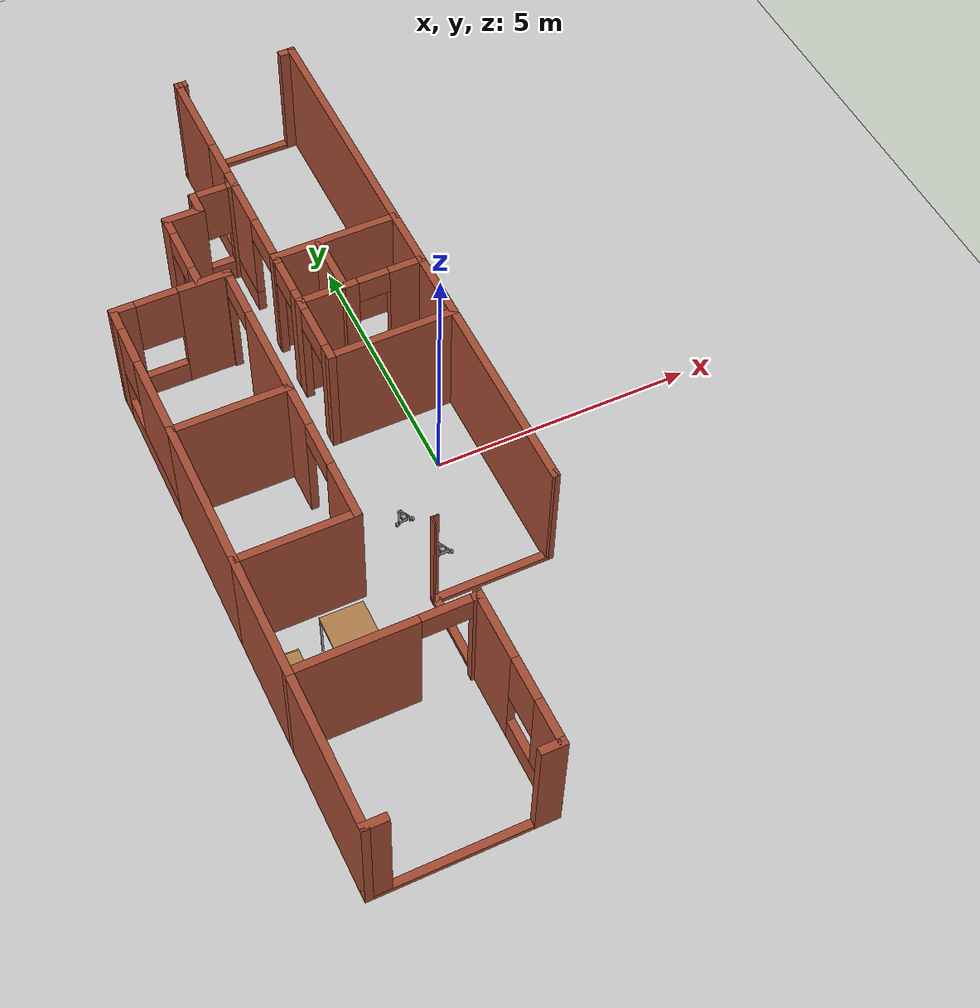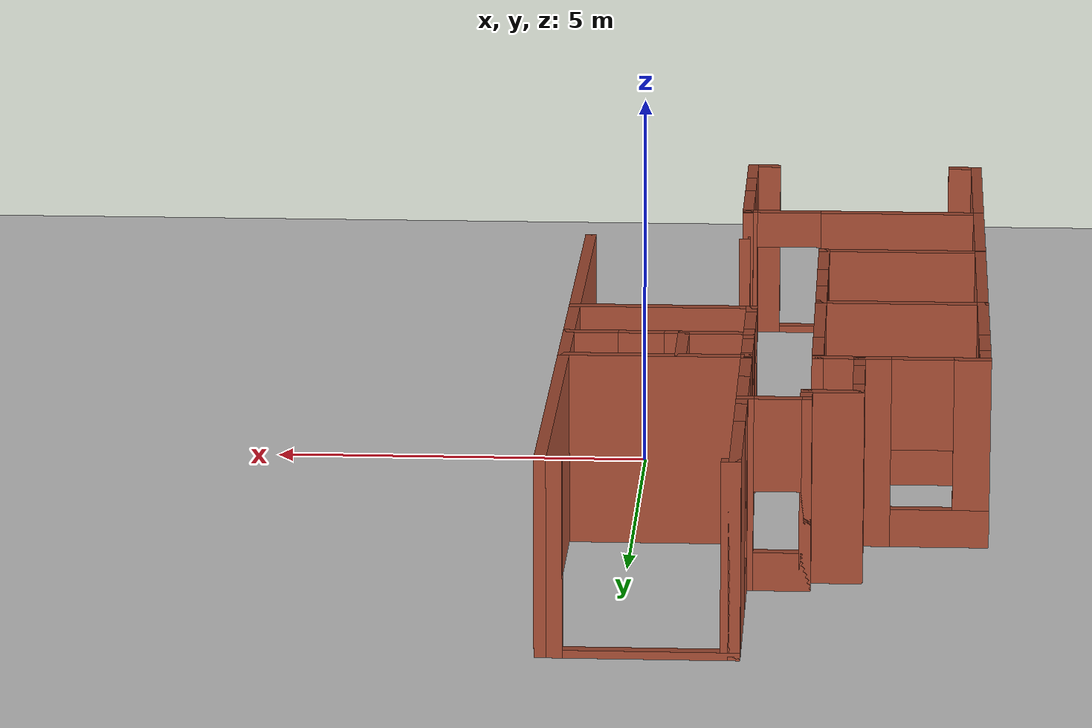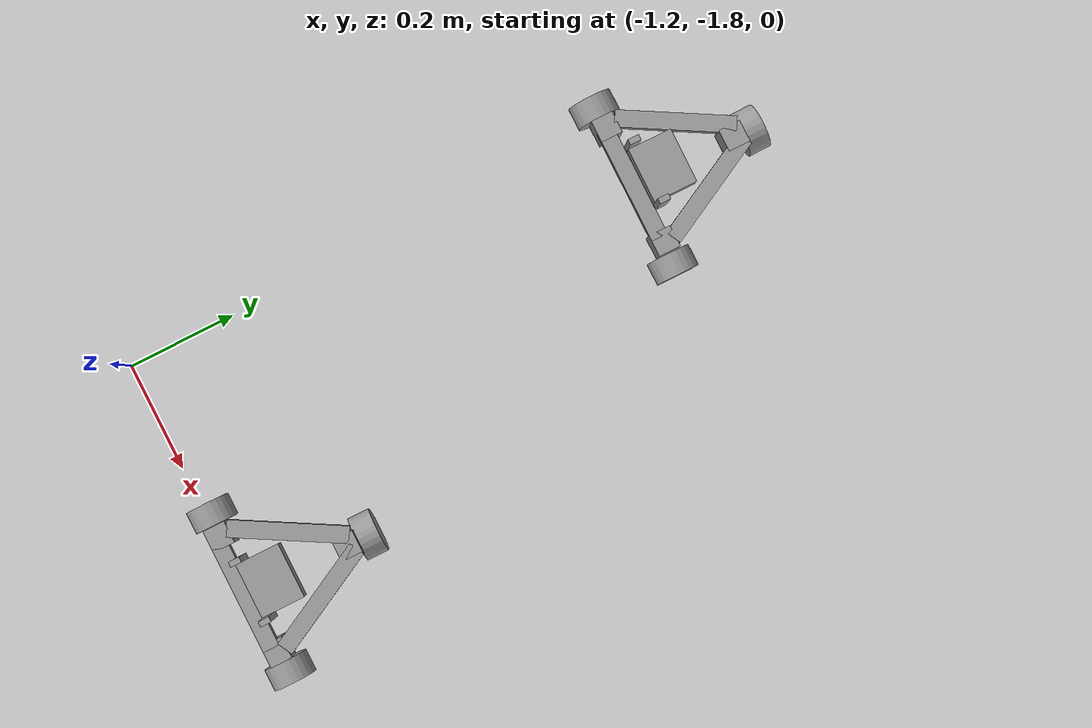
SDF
<sdf version="1.6">
 <world name="default">
  <plugin name="hello" filename="libhello.so"/>
  <light name="sun" type="directional">
   <pose>0 0 10 0 -0 0</pose>
   <diffuse>0.8 0.8 0.8 1</diffuse>
   <specular>0.1 0.1 0.1 1</specular>
   <attenuation>
    <range>1000</range>
    <constant>0.9</constant>
    <linear>0.01</linear>
    <quadratic>0.001</quadratic>
   </attenuation>
   <direction>-0.5 0.5 -1</direction>
  </light>
  <model name="ground_plane">
   <static>1</static>
   <link name="link">
    <collision name="collision">
     <geometry><plane><normal>0 0 1</normal><size>100 100</size></plane></geometry>
     <surface><friction><ode><mu>100</mu><mu2>50</mu2></ode></friction></surface>
    </collision>
    <visual name="visual">
     <cast_shadows>0</cast_shadows>
     <geometry><plane><normal>0 0 1</normal><size>100 100</size></plane></geometry>
     <material>
      <script><uri>file://media/materials/scripts/gazebo.material</uri><name>Gazebo/Grey</name></script>
     </material>
    </visual>
   </link>
  </model>
  <gravity>0 0 -9.8</gravity>
  <magnetic_field>6e-06 2.3e-05 -4.2e-05</magnetic_field>
  <atmosphere type="adiabatic"/>
  <physics name="default_physics" default="0" type="ode">
   <max_step_size>0.001</max_step_size>
   <real_time_factor>1</real_time_factor>
   <real_time_update_rate>1000</real_time_update_rate>
  </physics>
  <scene><ambient>0.4 0.4 0.4 1</ambient><background>0.7 0.7 0.7 1</background><shadows>1</shadows></scene>
  <spherical_coordinates>
   <surface_model>EARTH_WGS84</surface_model>
   <latitude_deg>0</latitude_deg>
   <longitude_deg>0</longitude_deg>
   <elevation>0</elevation>
   <heading_deg>0</heading_deg>
  </spherical_coordinates>
  <model name="Home">
   <pose>-1.82753 0.8177 0 0 -0 0</pose>
   <link name="Wall_10">
    <collision name="Wall_10_Collision">
     <geometry><box><size>1.3 0.15 2.5</size></box></geometry>
     <pose>0 0 1.25 0 -0 0</pose>
    </collision>
    <visual name="Wall_10_Visual">
     <pose>0 0 1.25 0 -0 0</pose>
     <geometry><box><size>1.3 0.15 2.5</size></box></geometry>
     <material>
      <script><uri>file://media/materials/scripts/gazebo.material</uri><name>Gazebo/Bricks</name></script>
      <ambient>1 1 1 1</ambient>
     </material>
    </visual>
    <pose>2.70626 2.39506 0 0 0 -1.5708</pose>
   </link>
   <link name="Wall_12">
    <pose>0.356264 2.39506 0 0 0 -1.5708</pose>
    <visual name="Wall_12_Visual_0">
     <pose>-0.527825 0 1.25 0 -0 0</pose>
     <geometry><box><size>0.24435 0.15 2.5</size></box></geometry>
     <material>
      <script><uri>file://media/materials/scripts/gazebo.material</uri><name>Gazebo/Bricks</name></script>
      <ambient>1 1 1 1</ambient>
     </material>
    </visual>
    <collision name="Wall_12_Collision_0">
     <geometry><box><size>0.24435 0.15 2.5</size></box></geometry>
     <pose>-0.527825 0 1.25 0 -0 0</pose>
    </collision>
    <visual name="Wall_12_Visual_1">
     <pose>0.472175 0 1.25 0 -0 0</pose>
     <geometry><box><size>0.35565 0.15 2.5</size></box></geometry>
     <material>
      <script><uri>file://media/materials/scripts/gazebo.material</uri><name>Gazebo/Bricks</name></script>
      <ambient>1 1 1 1</ambient>
     </material>
    </visual>
    <collision name="Wall_12_Collision_1">
     <geometry><box><size>0.35565 0.15 2.5</size></box></geometry>
     <pose>0.472175 0 1.25 0 -0 0</pose>
    </collision>
    <visual name="Wall_12_Visual_2">
     <pose>-0.05565 0 2.25 0 -0 0</pose>
     <geometry><box><size>0.7 0.15 0.5</size></box></geometry>
     <material>
      <script><uri>file://media/materials/scripts/gazebo.material</uri><name>Gazebo/Bricks</name></script>
      <ambient>1 1 1 1</ambient>
     </material>
    </visual>
    <collision name="Wall_12_Collision_2">
     <geometry><box><size>0.7 0.15 0.5</size></box></geometry>
     <pose>-0.05565 0 2.25 0 -0 0</pose>
    </collision>
   </link>
   <link name="Wall_14">
    <collision name="Wall_14_Collision">
     <geometry><box><size>1 0.15 2.5</size></box></geometry>
     <pose>0 0 1.25 0 -0 0</pose>
    </collision>
    <visual name="Wall_14_Visual">
     <pose>0 0 1.25 0 -0 0</pose>
     <geometry><box><size>1 0.15 2.5</size></box></geometry>
     <material>
      <script><uri>file://media/materials/scripts/gazebo.material</uri><name>Gazebo/Bricks</name></script>
      <ambient>1 1 1 1</ambient>
     </material>
    </visual>
    <pose>0.781264 1.82006 0 0 -0 0</pose>
   </link>
   <link name="Wall_15">
    <collision name="Wall_15_Collision">
     <geometry><box><size>1.25 0.15 2.5</size></box></geometry>
     <pose>0 0 1.25 0 -0 0</pose>
    </collision>
    <visual name="Wall_15_Visual">
     <pose>0 0 1.25 0 -0 0</pose>
     <geometry><box><size>1.25 0.15 2.5</size></box></geometry>
     <material>
      <script><uri>file://media/materials/scripts/gazebo.material</uri><name>Gazebo/Bricks</name></script>
      <ambient>1 1 1 1</ambient>
     </material>
    </visual>
    <pose>1.20626 2.37006 0 0 -0 1.5708</pose>
   </link>
   <link name="Wall_17">
    <pose>1.95626 1.82006 0 0 -0 0</pose>
    <visual name="Wall_17_Visual_0">
     <pose>-0.661575 0 1.25 0 -0 0</pose>
     <geometry><box><size>0.32685 0.15 2.5</size></box></geometry>
     <material>
      <script><uri>file://media/materials/scripts/gazebo.material</uri><name>Gazebo/Bricks</name></script>
      <ambient>1 1 1 1</ambient>
     </material>
    </visual>
    <collision name="Wall_17_Collision_0">
     <geometry><box><size>0.32685 0.15 2.5</size></box></geometry>
     <pose>-0.661575 0 1.25 0 -0 0</pose>
    </collision>
    <visual name="Wall_17_Visual_1">
     <pose>0.463425 0 1.25 0 -0 0</pose>
     <geometry><box><size>0.72315 0.15 2.5</size></box></geometry>
     <material>
      <script><uri>file://media/materials/scripts/gazebo.material</uri><name>Gazebo/Bricks</name></script>
      <ambient>1 1 1 1</ambient>
     </material>
    </visual>
    <collision name="Wall_17_Collision_1">
     <geometry><box><size>0.72315 0.15 2.5</size></box></geometry>
     <pose>0.463425 0 1.25 0 -0 0</pose>
    </collision>
    <visual name="Wall_17_Visual_2">
     <pose>-0.19815 0 2.25 0 -0 0</pose>
     <geometry><box><size>0.6 0.15 0.5</size></box></geometry>
     <material>
      <script><uri>file://media/materials/scripts/gazebo.material</uri><name>Gazebo/Bricks</name></script>
      <ambient>1 1 1 1</ambient>
     </material>
    </visual>
    <collision name="Wall_17_Collision_2">
     <geometry><box><size>0.6 0.15 0.5</size></box></geometry>
     <pose>-0.19815 0 2.25 0 -0 0</pose>
    </collision>
   </link>
   <link name="Wall_19">
    <collision name="Wall_19_Collision">
     <geometry><box><size>1.5 0.15 2.5</size></box></geometry>
     <pose>0 0 1.25 0 -0 0</pose>
    </collision>
    <visual name="Wall_19_Visual">
     <pose>0 0 1.25 0 -0 0</pose>
     <geometry><box><size>1.5 0.15 2.5</size></box></geometry>
     <material>
      <script><uri>file://media/materials/scripts/gazebo.material</uri><name>Gazebo/Bricks</name></script>
      <ambient>1 1 1 1</ambient>
     </material>
    </visual>
    <pose>2.70626 1.14506 0 0 0 -1.5708</pose>
   </link>
   <link name="Wall_20">
    <collision name="Wall_20_Collision">
     <geometry><box><size>2.5 0.15 2.5</size></box></geometry>
     <pose>0 0 1.25 0 -0 0</pose>
    </collision>
    <visual name="Wall_20_Visual">
     <pose>0 0 1.25 0 -0 0</pose>
     <geometry><box><size>2.5 0.15 2.5</size></box></geometry>
     <material>
      <script><uri>file://media/materials/scripts/gazebo.material</uri><name>Gazebo/Bricks</name></script>
      <ambient>1 1 1 1</ambient>
     </material>
    </visual>
    <pose>1.53126 0.470062 0 0 -0 3.14159</pose>
   </link>
   <link name="Wall_21">
    <pose>0.356264 1.14506 0 0 -0 1.5708</pose>
    <visual name="Wall_21_Visual_0">
     <pose>-0.588587 0 1.25 0 -0 0</pose>
     <geometry><box><size>0.322825 0.15 2.5</size></box></geometry>
     <material>
      <script><uri>file://media/materials/scripts/gazebo.material</uri><name>Gazebo/Bricks</name></script>
      <ambient>1 1 1 1</ambient>
     </material>
    </visual>
    <collision name="Wall_21_Collision_0">
     <geometry><box><size>0.322825 0.15 2.5</size></box></geometry>
     <pose>-0.588587 0 1.25 0 -0 0</pose>
    </collision>
    <visual name="Wall_21_Visual_1">
     <pose>0.611413 0 1.25 0 -0 0</pose>
     <geometry><box><size>0.277175 0.15 2.5</size></box></geometry>
     <material>
      <script><uri>file://media/materials/scripts/gazebo.material</uri><name>Gazebo/Bricks</name></script>
      <ambient>1 1 1 1</ambient>
     </material>
    </visual>
    <collision name="Wall_21_Collision_1">
     <geometry><box><size>0.277175 0.15 2.5</size></box></geometry>
     <pose>0.611413 0 1.25 0 -0 0</pose>
    </collision>
    <visual name="Wall_21_Visual_2">
     <pose>0.022825 0 2.25 0 -0 0</pose>
     <geometry><box><size>0.9 0.15 0.5</size></box></geometry>
     <material>
      <script><uri>file://media/materials/scripts/gazebo.material</uri><name>Gazebo/Bricks</name></script>
      <ambient>1 1 1 1</ambient>
     </material>
    </visual>
    <collision name="Wall_21_Collision_2">
     <geometry><box><size>0.9 0.15 0.5</size></box></geometry>
     <pose>0.022825 0 2.25 0 -0 0</pose>
    </collision>
   </link>
   <link name="Wall_23">
    <collision name="Wall_23_Collision">
     <geometry><box><size>4 0.15 2.5</size></box></geometry>
     <pose>0 0 1.25 0 -0 0</pose>
    </collision>
    <visual name="Wall_23_Visual">
     <pose>0 0 1.25 0 -0 0</pose>
     <geometry><box><size>4 0.15 2.5</size></box></geometry>
     <material>
      <script><uri>file://media/materials/scripts/gazebo.material</uri><name>Gazebo/Bricks</name></script>
      <ambient>1 1 1 1</ambient>
     </material>
    </visual>
    <pose>2.70626 -1.45494 0 0 0 -1.5708</pose>
   </link>
   <link name="Wall_24">
    <pose>1.63126 -3.37994 0 0 -0 3.14159</pose>
    <visual name="Wall_24_Visual_0">
     <pose>-1.10165 0 1.25 0 -0 0</pose>
     <geometry><box><size>0.0967 0.15 2.5</size></box></geometry>
     <material>
      <script><uri>file://media/materials/scripts/gazebo.material</uri><name>Gazebo/Bricks</name></script>
      <ambient>1 1 1 1</ambient>
     </material>
    </visual>
    <collision name="Wall_24_Collision_0">
     <geometry><box><size>0.0967 0.15 2.5</size></box></geometry>
     <pose>-1.10165 0 1.25 0 -0 0</pose>
    </collision>
    <visual name="Wall_24_Visual_1">
     <pose>0.04835 0 0.05 0 -0 0</pose>
     <geometry><box><size>2.2033 0.15 0.1</size></box></geometry>
     <material>
      <script><uri>file://media/materials/scripts/gazebo.material</uri><name>Gazebo/Bricks</name></script>
      <ambient>1 1 1 1</ambient>
     </material>
    </visual>
    <collision name="Wall_24_Collision_1">
     <geometry><box><size>2.2033 0.15 0.1</size></box></geometry>
     <pose>0.04835 0 0.05 0 -0 0</pose>
    </collision>
    <visual name="Wall_24_Visual_2">
     <pose>1.1335 0 1.3 0 -0 0</pose>
     <geometry><box><size>0.033 0.15 2.4</size></box></geometry>
     <material>
      <script><uri>file://media/materials/scripts/gazebo.material</uri><name>Gazebo/Bricks</name></script>
      <ambient>1 1 1 1</ambient>
     </material>
    </visual>
    <collision name="Wall_24_Collision_2">
     <geometry><box><size>0.033 0.15 2.4</size></box></geometry>
     <pose>1.1335 0 1.3 0 -0 0</pose>
    </collision>
   </link>
   <link name="Wall_26">
    <pose>-1.63126 2.97971 0 0 -0 3.14159</pose>
    <visual name="Wall_26_Visual_0">
     <pose>-0.638025 0 1.25 0 -0 0</pose>
     <geometry><box><size>1.02395 0.15 2.5</size></box></geometry>
     <material>
      <script><uri>file://media/materials/scripts/gazebo.material</uri><name>Gazebo/Bricks</name></script>
      <ambient>1 1 1 1</ambient>
     </material>
    </visual>
    <collision name="Wall_26_Collision_0">
     <geometry><box><size>1.02395 0.15 2.5</size></box></geometry>
     <pose>-0.638025 0 1.25 0 -0 0</pose>
    </collision>
    <visual name="Wall_26_Visual_1">
     <pose>0.511975 0 0.25 0 -0 0</pose>
     <geometry><box><size>1.27605 0.15 0.5</size></box></geometry>
     <material>
      <script><uri>file://media/materials/scripts/gazebo.material</uri><name>Gazebo/Bricks</name></script>
      <ambient>1 1 1 1</ambient>
     </material>
    </visual>
    <collision name="Wall_26_Collision_1">
     <geometry><box><size>1.27605 0.15 0.5</size></box></geometry>
     <pose>0.511975 0 0.25 0 -0 0</pose>
    </collision>
    <visual name="Wall_26_Visual_2">
     <pose>0.911975 0 1.5 0 -0 0</pose>
     <geometry><box><size>0.47605 0.15 2</size></box></geometry>
     <material>
      <script><uri>file://media/materials/scripts/gazebo.material</uri><name>Gazebo/Bricks</name></script>
      <ambient>1 1 1 1</ambient>
     </material>
    </visual>
    <collision name="Wall_26_Collision_2">
     <geometry><box><size>0.47605 0.15 2</size></box></geometry>
     <pose>0.911975 0 1.5 0 -0 0</pose>
    </collision>
    <visual name="Wall_26_Visual_3">
     <pose>0.27395 0 1.9 0 -0 0</pose>
     <geometry><box><size>0.8 0.15 1.2</size></box></geometry>
     <material>
      <script><uri>file://media/materials/scripts/gazebo.material</uri><name>Gazebo/Bricks</name></script>
      <ambient>1 1 1 1</ambient>
     </material>
    </visual>
    <collision name="Wall_26_Collision_3">
     <geometry><box><size>0.8 0.15 1.2</size></box></geometry>
     <pose>0.27395 0 1.9 0 -0 0</pose>
    </collision>
   </link>
   <link name="Wall_28">
    <pose>-2.70626 1.55471 0 0 0 -1.5708</pose>
    <visual name="Wall_28_Visual_0">
     <pose>-1.24591 0 1.25 0 -0 0</pose>
     <geometry><box><size>0.508175 0.15 2.5</size></box></geometry>
     <material>
      <script><uri>file://media/materials/scripts/gazebo.material</uri><name>Gazebo/Bricks</name></script>
      <ambient>1 1 1 1</ambient>
     </material>
    </visual>
    <collision name="Wall_28_Collision_0">
     <geometry><box><size>0.508175 0.15 2.5</size></box></geometry>
     <pose>-1.24591 0 1.25 0 -0 0</pose>
    </collision>
    <visual name="Wall_28_Visual_1">
     <pose>0.254087 0 0.25 0 -0 0</pose>
     <geometry><box><size>2.49182 0.15 0.5</size></box></geometry>
     <material>
      <script><uri>file://media/materials/scripts/gazebo.material</uri><name>Gazebo/Bricks</name></script>
      <ambient>1 1 1 1</ambient>
     </material>
    </visual>
    <collision name="Wall_28_Collision_1">
     <geometry><box><size>2.49182 0.15 0.5</size></box></geometry>
     <pose>0.254087 0 0.25 0 -0 0</pose>
    </collision>
    <visual name="Wall_28_Visual_2">
     <pose>0.654087 0 1.5 0 -0 0</pose>
     <geometry><box><size>1.69182 0.15 2</size></box></geometry>
     <material>
      <script><uri>file://media/materials/scripts/gazebo.material</uri><name>Gazebo/Bricks</name></script>
      <ambient>1 1 1 1</ambient>
     </material>
    </visual>
    <collision name="Wall_28_Collision_2">
     <geometry><box><size>1.69182 0.15 2</size></box></geometry>
     <pose>0.654087 0 1.5 0 -0 0</pose>
    </collision>
    <visual name="Wall_28_Visual_3">
     <pose>-0.591825 0 1.9 0 -0 0</pose>
     <geometry><box><size>0.8 0.15 1.2</size></box></geometry>
     <material>
      <script><uri>file://media/materials/scripts/gazebo.material</uri><name>Gazebo/Bricks</name></script>
      <ambient>1 1 1 1</ambient>
     </material>
    </visual>
    <collision name="Wall_28_Collision_3">
     <geometry><box><size>0.8 0.15 1.2</size></box></geometry>
     <pose>-0.591825 0 1.9 0 -0 0</pose>
    </collision>
   </link>
   <link name="Wall_29">
    <collision name="Wall_29_Collision">
     <geometry><box><size>2.3 0.15 2.5</size></box></geometry>
     <pose>0 0 1.25 0 -0 0</pose>
    </collision>
    <visual name="Wall_29_Visual">
     <pose>0 0 1.25 0 -0 0</pose>
     <geometry><box><size>2.3 0.15 2.5</size></box></geometry>
     <material>
      <script><uri>file://media/materials/scripts/gazebo.material</uri><name>Gazebo/Bricks</name></script>
      <ambient>1 1 1 1</ambient>
     </material>
    </visual>
    <pose>-1.63126 0.129712 0 0 -0 0</pose>
   </link>
   <link name="Wall_31">
    <pose>-0.556261 1.55471 0 0 -0 1.5708</pose>
    <visual name="Wall_31_Visual_0">
     <pose>-0.540225 0 1.25 0 -0 0</pose>
     <geometry><box><size>1.91955 0.15 2.5</size></box></geometry>
     <material>
      <script><uri>file://media/materials/scripts/gazebo.material</uri><name>Gazebo/Bricks</name></script>
      <ambient>1 1 1 1</ambient>
     </material>
    </visual>
    <collision name="Wall_31_Collision_0">
     <geometry><box><size>1.91955 0.15 2.5</size></box></geometry>
     <pose>-0.540225 0 1.25 0 -0 0</pose>
    </collision>
    <visual name="Wall_31_Visual_1">
     <pose>1.40978 0 1.25 0 -0 0</pose>
     <geometry><box><size>0.18045 0.15 2.5</size></box></geometry>
     <material>
      <script><uri>file://media/materials/scripts/gazebo.material</uri><name>Gazebo/Bricks</name></script>
      <ambient>1 1 1 1</ambient>
     </material>
    </visual>
    <collision name="Wall_31_Collision_1">
     <geometry><box><size>0.18045 0.15 2.5</size></box></geometry>
     <pose>1.40978 0 1.25 0 -0 0</pose>
    </collision>
    <visual name="Wall_31_Visual_2">
     <pose>0.86955 0 2.25 0 -0 0</pose>
     <geometry><box><size>0.9 0.15 0.5</size></box></geometry>
     <material>
      <script><uri>file://media/materials/scripts/gazebo.material</uri><name>Gazebo/Bricks</name></script>
      <ambient>1 1 1 1</ambient>
     </material>
    </visual>
    <collision name="Wall_31_Collision_2">
     <geometry><box><size>0.9 0.15 0.5</size></box></geometry>
     <pose>0.86955 0 2.25 0 -0 0</pose>
    </collision>
   </link>
   <link name="Wall_33">
    <collision name="Wall_33_Collision">
     <geometry><box><size>3 0.15 2.5</size></box></geometry>
     <pose>0 0 1.25 0 -0 0</pose>
    </collision>
    <visual name="Wall_33_Visual">
     <pose>0 0 1.25 0 -0 0</pose>
     <geometry><box><size>3 0.15 2.5</size></box></geometry>
     <material>
      <script><uri>file://media/materials/scripts/gazebo.material</uri><name>Gazebo/Bricks</name></script>
      <ambient>1 1 1 1</ambient>
     </material>
    </visual>
    <pose>-2.70626 -1.29529 0 0 0 -1.5708</pose>
   </link>
   <link name="Wall_34">
    <collision name="Wall_34_Collision">
     <geometry><box><size>2.3 0.15 2.5</size></box></geometry>
     <pose>0 0 1.25 0 -0 0</pose>
    </collision>
    <visual name="Wall_34_Visual">
     <pose>0 0 1.25 0 -0 0</pose>
     <geometry><box><size>2.3 0.15 2.5</size></box></geometry>
     <material>
      <script><uri>file://media/materials/scripts/gazebo.material</uri><name>Gazebo/Bricks</name></script>
      <ambient>1 1 1 1</ambient>
     </material>
    </visual>
    <pose>-1.63126 -2.72029 0 0 -0 0</pose>
   </link>
   <link name="Wall_36">
    <pose>-0.556261 -1.29529 0 0 -0 1.5708</pose>
    <visual name="Wall_36_Visual_0">
     <pose>-0.920437 0 1.25 0 -0 0</pose>
     <geometry><box><size>1.15912 0.15 2.5</size></box></geometry>
     <material>
      <script><uri>file://media/materials/scripts/gazebo.material</uri><name>Gazebo/Bricks</name></script>
      <ambient>1 1 1 1</ambient>
     </material>
    </visual>
    <collision name="Wall_36_Collision_0">
     <geometry><box><size>1.15912 0.15 2.5</size></box></geometry>
     <pose>-0.920437 0 1.25 0 -0 0</pose>
    </collision>
    <visual name="Wall_36_Visual_1">
     <pose>1.02956 0 1.25 0 -0 0</pose>
     <geometry><box><size>0.940875 0.15 2.5</size></box></geometry>
     <material>
      <script><uri>file://media/materials/scripts/gazebo.material</uri><name>Gazebo/Bricks</name></script>
      <ambient>1 1 1 1</ambient>
     </material>
    </visual>
    <collision name="Wall_36_Collision_1">
     <geometry><box><size>0.940875 0.15 2.5</size></box></geometry>
     <pose>1.02956 0 1.25 0 -0 0</pose>
    </collision>
    <visual name="Wall_36_Visual_2">
     <pose>0.109125 0 2.25 0 -0 0</pose>
     <geometry><box><size>0.9 0.15 0.5</size></box></geometry>
     <material>
      <script><uri>file://media/materials/scripts/gazebo.material</uri><name>Gazebo/Bricks</name></script>
      <ambient>1 1 1 1</ambient>
     </material>
    </visual>
    <collision name="Wall_36_Collision_2">
     <geometry><box><size>0.9 0.15 0.5</size></box></geometry>
     <pose>0.109125 0 2.25 0 -0 0</pose>
    </collision>
   </link>
   <link name="Wall_38">
    <collision name="Wall_38_Collision">
     <geometry><box><size>2.4 0.15 2.5</size></box></geometry>
     <pose>0 0 1.25 0 -0 0</pose>
    </collision>
    <visual name="Wall_38_Visual">
     <pose>0 0 1.25 0 -0 0</pose>
     <geometry><box><size>2.4 0.15 2.5</size></box></geometry>
     <material>
      <script><uri>file://media/materials/scripts/gazebo.material</uri><name>Gazebo/Bricks</name></script>
      <ambient>1 1 1 1</ambient>
     </material>
    </visual>
    <pose>-2.70622 -3.84517 0 0 0 -1.57076</pose>
   </link>
   <link name="Wall_40">
    <pose>-1.07519 -4.97006 0 0 -0 0</pose>
    <visual name="Wall_40_Visual_0">
     <pose>-0.554037 0 1.25 0 -0 0</pose>
     <geometry><box><size>2.30393 0.15 2.5</size></box></geometry>
     <material>
      <script><uri>file://media/materials/scripts/gazebo.material</uri><name>Gazebo/Bricks</name></script>
      <ambient>1 1 1 1</ambient>
     </material>
    </visual>
    <collision name="Wall_40_Collision_0">
     <geometry><box><size>2.30393 0.15 2.5</size></box></geometry>
     <pose>-0.554037 0 1.25 0 -0 0</pose>
    </collision>
    <visual name="Wall_40_Visual_1">
     <pose>1.60196 0 1.25 0 -0 0</pose>
     <geometry><box><size>0.208075 0.15 2.5</size></box></geometry>
     <material>
      <script><uri>file://media/materials/scripts/gazebo.material</uri><name>Gazebo/Bricks</name></script>
      <ambient>1 1 1 1</ambient>
     </material>
    </visual>
    <collision name="Wall_40_Collision_1">
     <geometry><box><size>0.208075 0.15 2.5</size></box></geometry>
     <pose>1.60196 0 1.25 0 -0 0</pose>
    </collision>
    <visual name="Wall_40_Visual_2">
     <pose>1.04792 0 2.25 0 -0 0</pose>
     <geometry><box><size>0.9 0.15 0.5</size></box></geometry>
     <material>
      <script><uri>file://media/materials/scripts/gazebo.material</uri><name>Gazebo/Bricks</name></script>
      <ambient>1 1 1 1</ambient>
     </material>
    </visual>
    <collision name="Wall_40_Collision_2">
     <geometry><box><size>0.9 0.15 0.5</size></box></geometry>
     <pose>1.04792 0 2.25 0 -0 0</pose>
    </collision>
   </link>
   <link name="Wall_42">
    <pose>0.556039 -4.175 0 0 -0 1.57051</pose>
    <visual name="Wall_42_Visual_0">
     <pose>-0.780496 0 1.25 0 -0 0</pose>
     <geometry><box><size>0.179133 0.15 2.5</size></box></geometry>
     <material>
      <script><uri>file://media/materials/scripts/gazebo.material</uri><name>Gazebo/Bricks</name></script>
      <ambient>1 1 1 1</ambient>
     </material>
    </visual>
    <collision name="Wall_42_Collision_0">
     <geometry><box><size>0.179133 0.15 2.5</size></box></geometry>
     <pose>-0.780496 0 1.25 0 -0 0</pose>
    </collision>
    <visual name="Wall_42_Visual_1">
     <pose>0.089567 0 0.05 0 -0 0</pose>
     <geometry><box><size>1.56099 0.15 0.1</size></box></geometry>
     <material>
      <script><uri>file://media/materials/scripts/gazebo.material</uri><name>Gazebo/Bricks</name></script>
      <ambient>1 1 1 1</ambient>
     </material>
    </visual>
    <collision name="Wall_42_Collision_1">
     <geometry><box><size>1.56099 0.15 0.1</size></box></geometry>
     <pose>0.089567 0 0.05 0 -0 0</pose>
    </collision>
    <visual name="Wall_42_Visual_2">
     <pose>0.859872 0 1.3 0 -0 0</pose>
     <geometry><box><size>0.020381 0.15 2.4</size></box></geometry>
     <material>
      <script><uri>file://media/materials/scripts/gazebo.material</uri><name>Gazebo/Bricks</name></script>
      <ambient>1 1 1 1</ambient>
     </material>
    </visual>
    <collision name="Wall_42_Collision_2">
     <geometry><box><size>0.020381 0.15 2.4</size></box></geometry>
     <pose>0.859872 0 1.3 0 -0 0</pose>
    </collision>
   </link>
   <link name="Wall_44">
    <collision name="Wall_44_Collision">
     <geometry><box><size>3 0.15 2.5</size></box></geometry>
     <pose>0 0 1.25 0 -0 0</pose>
    </collision>
    <visual name="Wall_44_Visual">
     <pose>0 0 1.25 0 -0 0</pose>
     <geometry><box><size>3 0.15 2.5</size></box></geometry>
     <material>
      <script><uri>file://media/materials/scripts/gazebo.material</uri><name>Gazebo/Bricks</name></script>
      <ambient>1 1 1 1</ambient>
     </material>
    </visual>
    <pose>-2.70619 -6.39506 0 0 0 -1.5708</pose>
   </link>
   <link name="Wall_46">
    <pose>0.555814 -6.39506 0 0 0 -1.5708</pose>
    <visual name="Wall_46_Visual_0">
     <pose>-0.836713 0 1.25 0 -0 0</pose>
     <geometry><box><size>1.32658 0.15 2.5</size></box></geometry>
     <material>
      <script><uri>file://media/materials/scripts/gazebo.material</uri><name>Gazebo/Bricks</name></script>
      <ambient>1 1 1 1</ambient>
     </material>
    </visual>
    <collision name="Wall_46_Collision_0">
     <geometry><box><size>1.32658 0.15 2.5</size></box></geometry>
     <pose>-0.836713 0 1.25 0 -0 0</pose>
    </collision>
    <visual name="Wall_46_Visual_1">
     <pose>0.663287 0 0.25 0 -0 0</pose>
     <geometry><box><size>1.67342 0.15 0.5</size></box></geometry>
     <material>
      <script><uri>file://media/materials/scripts/gazebo.material</uri><name>Gazebo/Bricks</name></script>
      <ambient>1 1 1 1</ambient>
     </material>
    </visual>
    <collision name="Wall_46_Collision_1">
     <geometry><box><size>1.67342 0.15 0.5</size></box></geometry>
     <pose>0.663287 0 0.25 0 -0 0</pose>
    </collision>
    <visual name="Wall_46_Visual_2">
     <pose>1.06329 0 1.5 0 -0 0</pose>
     <geometry><box><size>0.873425 0.15 2</size></box></geometry>
     <material>
      <script><uri>file://media/materials/scripts/gazebo.material</uri><name>Gazebo/Bricks</name></script>
      <ambient>1 1 1 1</ambient>
     </material>
    </visual>
    <collision name="Wall_46_Collision_2">
     <geometry><box><size>0.873425 0.15 2</size></box></geometry>
     <pose>1.06329 0 1.5 0 -0 0</pose>
    </collision>
    <visual name="Wall_46_Visual_3">
     <pose>0.226575 0 1.9 0 -0 0</pose>
     <geometry><box><size>0.8 0.15 1.2</size></box></geometry>
     <material>
      <script><uri>file://media/materials/scripts/gazebo.material</uri><name>Gazebo/Bricks</name></script>
      <ambient>1 1 1 1</ambient>
     </material>
    </visual>
    <collision name="Wall_46_Collision_3">
     <geometry><box><size>0.8 0.15 1.2</size></box></geometry>
     <pose>0.226575 0 1.9 0 -0 0</pose>
    </collision>
   </link>
   <link name="Wall_47">
    <pose>-1.07519 -7.82006 0 0 -0 3.14159</pose>
    <visual name="Wall_47_Visual_0">
     <pose>-1.46958 0 1.25 0 -0 0</pose>
     <geometry><box><size>0.47285 0.15 2.5</size></box></geometry>
     <material>
      <script><uri>file://media/materials/scripts/gazebo.material</uri><name>Gazebo/Bricks</name></script>
      <ambient>1 1 1 1</ambient>
     </material>
    </visual>
    <collision name="Wall_47_Collision_0">
     <geometry><box><size>0.47285 0.15 2.5</size></box></geometry>
     <pose>-1.46958 0 1.25 0 -0 0</pose>
    </collision>
    <visual name="Wall_47_Visual_1">
     <pose>0.236425 0 0.05 0 -0 0</pose>
     <geometry><box><size>2.93915 0.15 0.1</size></box></geometry>
     <material>
      <script><uri>file://media/materials/scripts/gazebo.material</uri><name>Gazebo/Bricks</name></script>
      <ambient>1 1 1 1</ambient>
     </material>
    </visual>
    <collision name="Wall_47_Collision_1">
     <geometry><box><size>2.93915 0.15 0.1</size></box></geometry>
     <pose>0.236425 0 0.05 0 -0 0</pose>
    </collision>
    <visual name="Wall_47_Visual_2">
     <pose>1.46643 0 1.3 0 -0 0</pose>
     <geometry><box><size>0.47915 0.15 2.4</size></box></geometry>
     <material>
      <script><uri>file://media/materials/scripts/gazebo.material</uri><name>Gazebo/Bricks</name></script>
      <ambient>1 1 1 1</ambient>
     </material>
    </visual>
    <collision name="Wall_47_Collision_2">
     <geometry><box><size>0.47915 0.15 2.4</size></box></geometry>
     <pose>1.46643 0 1.3 0 -0 0</pose>
    </collision>
   </link>
   <link name="Wall_5">
    <pose>0.356264 5.39506 0 0 0 -1.5708</pose>
    <visual name="Wall_5_Visual_0">
     <pose>-1.58466 0 1.25 0 -0 0</pose>
     <geometry><box><size>1.83068 0.15 2.5</size></box></geometry>
     <material>
      <script><uri>file://media/materials/scripts/gazebo.material</uri><name>Gazebo/Bricks</name></script>
      <ambient>1 1 1 1</ambient>
     </material>
    </visual>
    <collision name="Wall_5_Collision_0">
     <geometry><box><size>1.83068 0.15 2.5</size></box></geometry>
     <pose>-1.58466 0 1.25 0 -0 0</pose>
    </collision>
    <visual name="Wall_5_Visual_1">
     <pose>2.41818 0 1.25 0 -0 0</pose>
     <geometry><box><size>0.16365 0.15 2.5</size></box></geometry>
     <material>
      <script><uri>file://media/materials/scripts/gazebo.material</uri><name>Gazebo/Bricks</name></script>
      <ambient>1 1 1 1</ambient>
     </material>
    </visual>
    <collision name="Wall_5_Collision_1">
     <geometry><box><size>0.16365 0.15 2.5</size></box></geometry>
     <pose>2.41818 0 1.25 0 -0 0</pose>
    </collision>
    <visual name="Wall_5_Visual_2">
     <pose>0.383512 0 0.25 0 -0 0</pose>
     <geometry><box><size>2.10568 0.15 0.5</size></box></geometry>
     <material>
      <script><uri>file://media/materials/scripts/gazebo.material</uri><name>Gazebo/Bricks</name></script>
      <ambient>1 1 1 1</ambient>
     </material>
    </visual>
    <collision name="Wall_5_Collision_2">
     <geometry><box><size>2.10568 0.15 0.5</size></box></geometry>
     <pose>0.383512 0 0.25 0 -0 0</pose>
    </collision>
    <visual name="Wall_5_Visual_3">
     <pose>0.783512 0 1.5 0 -0 0</pose>
     <geometry><box><size>1.30567 0.15 2</size></box></geometry>
     <material>
      <script><uri>file://media/materials/scripts/gazebo.material</uri><name>Gazebo/Bricks</name></script>
      <ambient>1 1 1 1</ambient>
     </material>
    </visual>
    <collision name="Wall_5_Collision_3">
     <geometry><box><size>1.30567 0.15 2</size></box></geometry>
     <pose>0.783512 0 1.5 0 -0 0</pose>
    </collision>
    <visual name="Wall_5_Visual_4">
     <pose>-0.269325 0 1.9 0 -0 0</pose>
     <geometry><box><size>0.8 0.15 1.2</size></box></geometry>
     <material>
      <script><uri>file://media/materials/scripts/gazebo.material</uri><name>Gazebo/Bricks</name></script>
      <ambient>1 1 1 1</ambient>
     </material>
    </visual>
    <collision name="Wall_5_Collision_4">
     <geometry><box><size>0.8 0.15 1.2</size></box></geometry>
     <pose>-0.269325 0 1.9 0 -0 0</pose>
    </collision>
    <visual name="Wall_5_Visual_5">
     <pose>1.88635 0 2.25 0 -0 0</pose>
     <geometry><box><size>0.9 0.15 0.5</size></box></geometry>
     <material>
      <script><uri>file://media/materials/scripts/gazebo.material</uri><name>Gazebo/Bricks</name></script>
      <ambient>1 1 1 1</ambient>
     </material>
    </visual>
    <collision name="Wall_5_Collision_5">
     <geometry><box><size>0.9 0.15 0.5</size></box></geometry>
     <pose>1.88635 0 2.25 0 -0 0</pose>
    </collision>
   </link>
   <link name="Wall_50">
    <pose>-0.044186 4.96994 0 0 -0 3.14159</pose>
    <visual name="Wall_50_Visual_0">
     <pose>-0.3629 0 1.25 0 -0 0</pose>
     <geometry><box><size>0.2242 0.15 2.5</size></box></geometry>
     <material>
      <script><uri>file://media/materials/scripts/gazebo.material</uri><name>Gazebo/Bricks</name></script>
      <ambient>1 1 1 1</ambient>
     </material>
    </visual>
    <collision name="Wall_50_Collision_0">
     <geometry><box><size>0.2242 0.15 2.5</size></box></geometry>
     <pose>-0.3629 0 1.25 0 -0 0</pose>
    </collision>
    <visual name="Wall_50_Visual_1">
     <pose>0.1121 0 0.25 0 -0 0</pose>
     <geometry><box><size>0.7258 0.15 0.5</size></box></geometry>
     <material>
      <script><uri>file://media/materials/scripts/gazebo.material</uri><name>Gazebo/Bricks</name></script>
      <ambient>1 1 1 1</ambient>
     </material>
    </visual>
    <collision name="Wall_50_Collision_1">
     <geometry><box><size>0.7258 0.15 0.5</size></box></geometry>
     <pose>0.1121 0 0.25 0 -0 0</pose>
    </collision>
    <visual name="Wall_50_Visual_2">
     <pose>0.4121 0 1.5 0 -0 0</pose>
     <geometry><box><size>0.1258 0.15 2</size></box></geometry>
     <material>
      <script><uri>file://media/materials/scripts/gazebo.material</uri><name>Gazebo/Bricks</name></script>
      <ambient>1 1 1 1</ambient>
     </material>
    </visual>
    <collision name="Wall_50_Collision_2">
     <geometry><box><size>0.1258 0.15 2</size></box></geometry>
     <pose>0.4121 0 1.5 0 -0 0</pose>
    </collision>
    <visual name="Wall_50_Visual_3">
     <pose>0.0492 0 1.9 0 -0 0</pose>
     <geometry><box><size>0.6 0.15 1.2</size></box></geometry>
     <material>
      <script><uri>file://media/materials/scripts/gazebo.material</uri><name>Gazebo/Bricks</name></script>
      <ambient>1 1 1 1</ambient>
     </material>
    </visual>
    <collision name="Wall_50_Collision_3">
     <geometry><box><size>0.6 0.15 1.2</size></box></geometry>
     <pose>0.0492 0 1.9 0 -0 0</pose>
    </collision>
   </link>
   <link name="Wall_52">
    <collision name="Wall_52_Collision">
     <geometry><box><size>0.5 0.15 2.5</size></box></geometry>
     <pose>0 0 1.25 0 -0 0</pose>
    </collision>
    <visual name="Wall_52_Visual">
     <pose>0 0 1.25 0 -0 0</pose>
     <geometry><box><size>0.5 0.15 2.5</size></box></geometry>
     <material>
      <script><uri>file://media/materials/scripts/gazebo.material</uri><name>Gazebo/Bricks</name></script>
      <ambient>1 1 1 1</ambient>
     </material>
    </visual>
    <pose>-0.444186 4.79494 0 0 0 -1.5708</pose>
   </link>
   <link name="Wall_53">
    <collision name="Wall_53_Collision">
     <geometry><box><size>0.8 0.15 2.5</size></box></geometry>
     <pose>0 0 1.25 0 -0 0</pose>
    </collision>
    <visual name="Wall_53_Visual">
     <pose>0 0 1.25 0 -0 0</pose>
     <geometry><box><size>0.8 0.15 2.5</size></box></geometry>
     <material>
      <script><uri>file://media/materials/scripts/gazebo.material</uri><name>Gazebo/Bricks</name></script>
      <ambient>1 1 1 1</ambient>
     </material>
    </visual>
    <pose>-0.769186 4.61994 0 0 -0 3.14159</pose>
   </link>
   <link name="Wall_55">
    <pose>-1.09419 3.81994 0 0 0 -1.5708</pose>
    <visual name="Wall_55_Visual_0">
     <pose>-0.658975 0 1.25 0 -0 0</pose>
     <geometry><box><size>0.43205 0.15 2.5</size></box></geometry>
     <material>
      <script><uri>file://media/materials/scripts/gazebo.material</uri><name>Gazebo/Bricks</name></script>
      <ambient>1 1 1 1</ambient>
     </material>
    </visual>
    <collision name="Wall_55_Collision_0">
     <geometry><box><size>0.43205 0.15 2.5</size></box></geometry>
     <pose>-0.658975 0 1.25 0 -0 0</pose>
    </collision>
    <visual name="Wall_55_Visual_1">
     <pose>0.666025 0 1.25 0 -0 0</pose>
     <geometry><box><size>0.41795 0.15 2.5</size></box></geometry>
     <material>
      <script><uri>file://media/materials/scripts/gazebo.material</uri><name>Gazebo/Bricks</name></script>
      <ambient>1 1 1 1</ambient>
     </material>
    </visual>
    <collision name="Wall_55_Collision_1">
     <geometry><box><size>0.41795 0.15 2.5</size></box></geometry>
     <pose>0.666025 0 1.25 0 -0 0</pose>
    </collision>
    <visual name="Wall_55_Visual_2">
     <pose>0.00705 0 2.25 0 -0 0</pose>
     <geometry><box><size>0.9 0.15 0.5</size></box></geometry>
     <material>
      <script><uri>file://media/materials/scripts/gazebo.material</uri><name>Gazebo/Bricks</name></script>
      <ambient>1 1 1 1</ambient>
     </material>
    </visual>
    <collision name="Wall_55_Collision_2">
     <geometry><box><size>0.9 0.15 0.5</size></box></geometry>
     <pose>0.00705 0 2.25 0 -0 0</pose>
    </collision>
   </link>
   <link name="Wall_6">
    <collision name="Wall_6_Collision">
     <geometry><box><size>2.5 0.15 2.5</size></box></geometry>
     <pose>0 0 1.25 0 -0 0</pose>
    </collision>
    <visual name="Wall_6_Visual">
     <pose>0 0 1.25 0 -0 0</pose>
     <geometry><box><size>2.5 0.15 2.5</size></box></geometry>
     <material>
      <script><uri>file://media/materials/scripts/gazebo.material</uri><name>Gazebo/Bricks</name></script>
      <ambient>1 1 1 1</ambient>
     </material>
    </visual>
    <pose>1.53126 2.97006 0 0 -0 0</pose>
   </link>
   <link name="Wall_7">
    <collision name="Wall_7_Collision">
     <geometry><box><size>5 0.15 2.5</size></box></geometry>
     <pose>0 0 1.25 0 -0 0</pose>
    </collision>
    <visual name="Wall_7_Visual">
     <pose>0 0 1.25 0 -0 0</pose>
     <geometry><box><size>5 0.15 2.5</size></box></geometry>
     <material>
      <script><uri>file://media/materials/scripts/gazebo.material</uri><name>Gazebo/Bricks</name></script>
      <ambient>1 1 1 1</ambient>
     </material>
    </visual>
    <pose>2.70626 5.39506 0 0 -0 1.5708</pose>
   </link>
   <link name="Wall_8">
    <pose>1.53126 7.82006 0 0 -0 3.14159</pose>
    <visual name="Wall_8_Visual_0">
     <pose>-1.07771 0 1.25 0 -0 0</pose>
     <geometry><box><size>0.344584 0.15 2.5</size></box></geometry>
     <material>
      <script><uri>file://media/materials/scripts/gazebo.material</uri><name>Gazebo/Bricks</name></script>
      <ambient>1 1 1 1</ambient>
     </material>
    </visual>
    <collision name="Wall_8_Collision_0">
     <geometry><box><size>0.344584 0.15 2.5</size></box></geometry>
     <pose>-1.07771 0 1.25 0 -0 0</pose>
    </collision>
    <visual name="Wall_8_Visual_1">
     <pose>0.172292 0 0.05 0 -0 0</pose>
     <geometry><box><size>2.15542 0.15 0.1</size></box></geometry>
     <material>
      <script><uri>file://media/materials/scripts/gazebo.material</uri><name>Gazebo/Bricks</name></script>
      <ambient>1 1 1 1</ambient>
     </material>
    </visual>
    <collision name="Wall_8_Collision_1">
     <geometry><box><size>2.15542 0.15 0.1</size></box></geometry>
     <pose>0.172292 0 0.05 0 -0 0</pose>
    </collision>
    <visual name="Wall_8_Visual_2">
     <pose>1.12837 0 1.3 0 -0 0</pose>
     <geometry><box><size>0.243264 0.15 2.4</size></box></geometry>
     <material>
      <script><uri>file://media/materials/scripts/gazebo.material</uri><name>Gazebo/Bricks</name></script>
      <ambient>1 1 1 1</ambient>
     </material>
    </visual>
    <collision name="Wall_8_Collision_2">
     <geometry><box><size>0.243264 0.15 2.4</size></box></geometry>
     <pose>1.12837 0 1.3 0 -0 0</pose>
    </collision>
   </link>
   <static>1</static>
  </model>
  <model name="table">
   <static>0</static>
   <link name="link">
    <collision name="surface">
     <pose>0 0 1 0 -0 0</pose>
     <geometry><box><size>1.5 0.8 0.03</size></box></geometry>
     <surface><friction><ode><mu>0.6</mu><mu2>0.6</mu2></ode></friction></surface>
    </collision>
    <visual name="visual1">
     <pose>0 0 1 0 -0 0</pose>
     <geometry><box><size>1.4 0.8 0.04</size></box></geometry>
     <material>
      <script><uri>file://media/materials/scripts/gazebo.material</uri><name>Gazebo/Wood</name></script>
     </material>
    </visual>
    <collision name="front_left_leg">
     <pose>0.68 0.38 0.5 0 -0 0</pose>
     <geometry><cylinder><radius>0.02</radius><length>1</length></cylinder></geometry>
    </collision>
    <visual name="front_left_leg">
     <pose>0.68 0.38 0.5 0 -0 0</pose>
     <geometry><cylinder><radius>0.02</radius><length>1</length></cylinder></geometry>
     <material>
      <script><uri>file://media/materials/scripts/gazebo.material</uri><name>Gazebo/Grey</name></script>
     </material>
    </visual>
    <collision name="front_right_leg">
     <pose>0.68 -0.38 0.5 0 -0 0</pose>
     <geometry><cylinder><radius>0.02</radius><length>1</length></cylinder></geometry>
    </collision>
    <visual name="front_right_leg">
     <pose>0.68 -0.38 0.5 0 -0 0</pose>
     <geometry><cylinder><radius>0.02</radius><length>1</length></cylinder></geometry>
     <material>
      <script><uri>file://media/materials/scripts/gazebo.material</uri><name>Gazebo/Grey</name></script>
     </material>
    </visual>
    <collision name="back_right_leg">
     <pose>-0.68 -0.38 0.5 0 -0 0</pose>
     <geometry><cylinder><radius>0.02</radius><length>1</length></cylinder></geometry>
    </collision>
    <visual name="back_right_leg">
     <pose>-0.68 -0.38 0.5 0 -0 0</pose>
     <geometry><cylinder><radius>0.02</radius><length>1</length></cylinder></geometry>
     <material>
      <script><uri>file://media/materials/scripts/gazebo.material</uri><name>Gazebo/Grey</name></script>
     </material>
    </visual>
    <collision name="back_left_leg">
     <pose>-0.68 0.38 0.5 0 -0 0</pose>
     <geometry><cylinder><radius>0.02</radius><length>1</length></cylinder></geometry>
    </collision>
    <visual name="back_left_leg">
     <pose>-0.68 0.38 0.5 0 -0 0</pose>
     <geometry><cylinder><radius>0.02</radius><length>1</length></cylinder></geometry>
     <material>
      <script><uri>file://media/materials/scripts/gazebo.material</uri><name>Gazebo/Grey</name></script>
     </material>
    </visual>
    <inertial>
     <inertia><ixx>1</ixx><ixy>0</ixy><ixz>0</ixz><iyy>1</iyy><iyz>0</iyz><izz>1</izz></inertia>
     <mass>1</mass>
    </inertial>
   </link>
   <pose>-3.04038 -3.32569 0.001355 -0.000107 0.001878 1.56191</pose>
  </model>
  <model name="bookshelf">
   <static>1</static>
   <link name="link">
    <inertial><mass>1</mass></inertial>
    <collision name="back">
     <pose>0 0.005 0.6 0 -0 0</pose>
     <geometry><box><size>0.9 0.01 1.2</size></box></geometry>
    </collision>
    <visual name="visual1">
     <pose>0 0.005 0.6 0 -0 0</pose>
     <geometry><box><size>0.9 0.01 1.2</size></box></geometry>
     <material>
      <script><uri>file://media/materials/scripts/gazebo.material</uri><name>Gazebo/Wood</name></script>
     </material>
    </visual>
    <collision name="left_side">
     <pose>0.45 -0.195 0.6 0 -0 0</pose>
     <geometry><box><size>0.02 0.4 1.2</size></box></geometry>
    </collision>
    <visual name="visual2">
     <pose>0.45 -0.195 0.6 0 -0 0</pose>
     <geometry><box><size>0.02 0.4 1.2</size></box></geometry>
     <material>
      <script><uri>file://media/materials/scripts/gazebo.material</uri><name>Gazebo/Wood</name></script>
     </material>
    </visual>
    <collision name="right_side">
     <pose>-0.45 -0.195 0.6 0 -0 0</pose>
     <geometry><box><size>0.02 0.4 1.2</size></box></geometry>
    </collision>
    <visual name="visual3">
     <pose>-0.45 -0.195 0.6 0 -0 0</pose>
     <geometry><box><size>0.02 0.4 1.2</size></box></geometry>
     <material>
      <script><uri>file://media/materials/scripts/gazebo.material</uri><name>Gazebo/Wood</name></script>
     </material>
    </visual>
    <collision name="bottom">
     <pose>0 -0.195 0.03 0 -0 0</pose>
     <geometry><box><size>0.88 0.4 0.06</size></box></geometry>
    </collision>
    <visual name="visual4">
     <pose>0 -0.195 0.03 0 -0 0</pose>
     <geometry><box><size>0.88 0.4 0.06</size></box></geometry>
     <material>
      <script><uri>file://media/materials/scripts/gazebo.material</uri><name>Gazebo/Wood</name></script>
     </material>
    </visual>
    <collision name="top">
     <pose>0 -0.195 1.19 0 -0 0</pose>
     <geometry><box><size>0.88 0.4 0.02</size></box></geometry>
    </collision>
    <visual name="visual5">
     <pose>0 -0.195 1.19 0 -0 0</pose>
     <geometry><box><size>0.88 0.4 0.02</size></box></geometry>
     <material>
      <script><uri>file://media/materials/scripts/gazebo.material</uri><name>Gazebo/Wood</name></script>
     </material>
    </visual>
    <collision name="low_shelf">
     <pose>0 -0.195 0.43 0 -0 0</pose>
     <geometry><box><size>0.88 0.4 0.02</size></box></geometry>
    </collision>
    <visual name="visual6">
     <pose>0 -0.195 0.43 0 -0 0</pose>
     <geometry><box><size>0.88 0.4 0.02</size></box></geometry>
     <material>
      <script><uri>file://media/materials/scripts/gazebo.material</uri><name>Gazebo/Wood</name></script>
     </material>
    </visual>
    <collision name="high_shelf">
     <pose>0 -0.195 0.8 0 -0 0</pose>
     <geometry><box><size>0.88 0.4 0.02</size></box></geometry>
    </collision>
    <visual name="visual7">
     <pose>0 -0.195 0.8 0 -0 0</pose>
     <geometry><box><size>0.88 0.4 0.02</size></box></geometry>
     <material>
      <script><uri>file://media/materials/scripts/gazebo.material</uri><name>Gazebo/Wood</name></script>
     </material>
    </visual>
   </link>
   <pose>-4.40969 -3.5576 0 0 -0 1.51749</pose>
  </model>
  <model name="Kaya">
   <link name="link_0">
    <pose>-0.003284 -0.064713 0.005909 0 -0 0</pose>
    <inertial>
     <mass>1</mass>
     <inertia>
      <ixx>0.166667</ixx>
      <ixy>0</ixy>
      <ixz>0</ixz>
      <iyy>0.166667</iyy>
      <iyz>0</iyz>
      <izz>0.166667</izz>
     </inertia>
    </inertial>
    <visual name="visual">
     <geometry><box><size>0.21 0.03 0.02</size></box></geometry>
     <material>
      <lighting>1</lighting>
      <script><uri>file://media/materials/scripts/gazebo.material</uri><name>Gazebo/Grey</name></script>
      <ambient>0.3 0.3 0.3 1</ambient>
      <diffuse>0.7 0.7 0.7 1</diffuse>
      <specular>0.01 0.01 0.01 1</specular>
      <emissive>0 0 0 1</emissive>
      <shader type="vertex"><normal_map>__default__</normal_map></shader>
     </material>
    </visual>
    <collision name="collision">
     <geometry><box><size>0.21 0.03 0.02</size></box></geometry>
     <surface>
      <friction>
       <ode><mu>1</mu><mu2>1</mu2><fdir1>0 0 0</fdir1><slip1>0</slip1><slip2>0</slip2></ode>
       <torsional>
        <coefficient>1</coefficient>
        <patch_radius>0</patch_radius>
        <surface_radius>0</surface_radius>
        <use_patch_radius>1</use_patch_radius>
        <ode><slip>0</slip></ode>
       </torsional>
      </friction>
      <bounce><restitution_coefficient>0</restitution_coefficient><threshold>1e+06</threshold></bounce>
      <contact>
       <collide_without_contact>0</collide_without_contact>
       <collide_without_contact_bitmask>1</collide_without_contact_bitmask>
       <collide_bitmask>1</collide_bitmask>
       <ode>
        <soft_cfm>0</soft_cfm>
        <soft_erp>0.2</soft_erp>
        <kp>1e+13</kp>
        <kd>1</kd>
        <max_vel>0.01</max_vel>
        <min_depth>0</min_depth>
       </ode>
       <bullet>
        <split_impulse>1</split_impulse>
        <split_impulse_penetration_threshold>-0.01</split_impulse_penetration_threshold>
        <soft_cfm>0</soft_cfm>
        <soft_erp>0.2</soft_erp>
        <kp>1e+13</kp>
        <kd>1</kd>
       </bullet>
      </contact>
     </surface>
    </collision>
   </link>
   <link name="link_0_clone">
    <pose>0.063805 0.048952 0.005909 0 0 -1.08918</pose>
    <inertial>
     <mass>1</mass>
     <inertia>
      <ixx>0.166667</ixx>
      <ixy>0</ixy>
      <ixz>0</ixz>
      <iyy>0.166667</iyy>
      <iyz>0</iyz>
      <izz>0.166667</izz>
     </inertia>
    </inertial>
    <visual name="visual">
     <geometry><box><size>0.21 0.03 0.02</size></box></geometry>
     <material>
      <lighting>1</lighting>
      <script><uri>file://media/materials/scripts/gazebo.material</uri><name>Gazebo/Grey</name></script>
      <ambient>0.3 0.3 0.3 1</ambient>
      <diffuse>0.7 0.7 0.7 1</diffuse>
      <specular>0.01 0.01 0.01 1</specular>
      <emissive>0 0 0 1</emissive>
      <shader type="vertex"><normal_map>__default__</normal_map></shader>
     </material>
    </visual>
    <collision name="collision">
     <geometry><box><size>0.21 0.03 0.02</size></box></geometry>
     <surface>
      <friction>
       <ode><mu>1</mu><mu2>1</mu2><fdir1>0 0 0</fdir1><slip1>0</slip1><slip2>0</slip2></ode>
       <torsional>
        <coefficient>1</coefficient>
        <patch_radius>0</patch_radius>
        <surface_radius>0</surface_radius>
        <use_patch_radius>1</use_patch_radius>
        <ode><slip>0</slip></ode>
       </torsional>
      </friction>
      <bounce><restitution_coefficient>0</restitution_coefficient><threshold>1e+06</threshold></bounce>
      <contact>
       <collide_without_contact>0</collide_without_contact>
       <collide_without_contact_bitmask>1</collide_without_contact_bitmask>
       <collide_bitmask>1</collide_bitmask>
       <ode>
        <soft_cfm>0</soft_cfm>
        <soft_erp>0.2</soft_erp>
        <kp>1e+13</kp>
        <kd>1</kd>
        <max_vel>0.01</max_vel>
        <min_depth>0</min_depth>
       </ode>
       <bullet>
        <split_impulse>1</split_impulse>
        <split_impulse_penetration_threshold>-0.01</split_impulse_penetration_threshold>
        <soft_cfm>0</soft_cfm>
        <soft_erp>0.2</soft_erp>
        <kp>1e+13</kp>
        <kd>1</kd>
       </bullet>
      </contact>
     </surface>
    </collision>
   </link>
   <link name="link_0_clone_clone">
    <pose>-0.063575 0.049785 0.005909 0 0 -2.0892</pose>
    <inertial>
     <mass>1</mass>
     <inertia>
      <ixx>0.166667</ixx>
      <ixy>0</ixy>
      <ixz>0</ixz>
      <iyy>0.166667</iyy>
      <iyz>0</iyz>
      <izz>0.166667</izz>
     </inertia>
    </inertial>
    <visual name="visual">
     <geometry><box><size>0.21 0.03 0.02</size></box></geometry>
     <material>
      <lighting>1</lighting>
      <script><uri>file://media/materials/scripts/gazebo.material</uri><name>Gazebo/Grey</name></script>
      <ambient>0.3 0.3 0.3 1</ambient>
      <diffuse>0.7 0.7 0.7 1</diffuse>
      <specular>0.01 0.01 0.01 1</specular>
      <emissive>0 0 0 1</emissive>
      <shader type="vertex"><normal_map>__default__</normal_map></shader>
     </material>
    </visual>
    <collision name="collision">
     <geometry><box><size>0.21 0.03 0.02</size></box></geometry>
     <surface>
      <friction>
       <ode><mu>1</mu><mu2>1</mu2><fdir1>0 0 0</fdir1><slip1>0</slip1><slip2>0</slip2></ode>
       <torsional>
        <coefficient>1</coefficient>
        <patch_radius>0</patch_radius>
        <surface_radius>0</surface_radius>
        <use_patch_radius>1</use_patch_radius>
        <ode><slip>0</slip></ode>
       </torsional>
      </friction>
      <bounce><restitution_coefficient>0</restitution_coefficient><threshold>1e+06</threshold></bounce>
      <contact>
       <collide_without_contact>0</collide_without_contact>
       <collide_without_contact_bitmask>1</collide_without_contact_bitmask>
       <collide_bitmask>1</collide_bitmask>
       <ode>
        <soft_cfm>0</soft_cfm>
        <soft_erp>0.2</soft_erp>
        <kp>1e+13</kp>
        <kd>1</kd>
        <max_vel>0.01</max_vel>
        <min_depth>0</min_depth>
       </ode>
       <bullet>
        <split_impulse>1</split_impulse>
        <split_impulse_penetration_threshold>-0.01</split_impulse_penetration_threshold>
        <soft_cfm>0</soft_cfm>
        <soft_erp>0.2</soft_erp>
        <kp>1e+13</kp>
        <kd>1</kd>
       </bullet>
      </contact>
     </surface>
    </collision>
   </link>
   <link name="link_2">
    <pose>0.003786 0.128421 -0.019091 0 -0 0</pose>
    <inertial>
     <mass>1</mass>
     <inertia>
      <ixx>0.166667</ixx>
      <ixy>0</ixy>
      <ixz>0</ixz>
      <iyy>0.166667</iyy>
      <iyz>0</iyz>
      <izz>0.166667</izz>
     </inertia>
    </inertial>
    <visual name="visual">
     <geometry><box><size>0.04 0.04 0.07</size></box></geometry>
     <material>
      <lighting>1</lighting>
      <script><uri>file://media/materials/scripts/gazebo.material</uri><name>Gazebo/Grey</name></script>
      <ambient>0.3 0.3 0.3 1</ambient>
      <diffuse>0.7 0.7 0.7 1</diffuse>
      <specular>0.01 0.01 0.01 1</specular>
      <emissive>0 0 0 1</emissive>
      <shader type="vertex"><normal_map>__default__</normal_map></shader>
     </material>
    </visual>
    <collision name="collision">
     <geometry><box><size>0.04 0.04 0.07</size></box></geometry>
     <surface>
      <friction>
       <ode><mu>1</mu><mu2>1</mu2><fdir1>0 0 0</fdir1><slip1>0</slip1><slip2>0</slip2></ode>
       <torsional>
        <coefficient>1</coefficient>
        <patch_radius>0</patch_radius>
        <surface_radius>0</surface_radius>
        <use_patch_radius>1</use_patch_radius>
        <ode><slip>0</slip></ode>
       </torsional>
      </friction>
      <bounce><restitution_coefficient>0</restitution_coefficient><threshold>1e+06</threshold></bounce>
      <contact>
       <collide_without_contact>0</collide_without_contact>
       <collide_without_contact_bitmask>1</collide_without_contact_bitmask>
       <collide_bitmask>1</collide_bitmask>
       <ode>
        <soft_cfm>0</soft_cfm>
        <soft_erp>0.2</soft_erp>
        <kp>1e+13</kp>
        <kd>1</kd>
        <max_vel>0.01</max_vel>
        <min_depth>0</min_depth>
       </ode>
       <bullet>
        <split_impulse>1</split_impulse>
        <split_impulse_penetration_threshold>-0.01</split_impulse_penetration_threshold>
        <soft_cfm>0</soft_cfm>
        <soft_erp>0.2</soft_erp>
        <kp>1e+13</kp>
        <kd>1</kd>
       </bullet>
      </contact>
     </surface>
    </collision>
   </link>
   <link name="link_2_clone">
    <pose>0.110929 -0.059858 -0.019091 0 -0 0</pose>
    <inertial>
     <mass>1</mass>
     <inertia>
      <ixx>0.166667</ixx>
      <ixy>0</ixy>
      <ixz>0</ixz>
      <iyy>0.166667</iyy>
      <iyz>0</iyz>
      <izz>0.166667</izz>
     </inertia>
    </inertial>
    <visual name="visual">
     <geometry><box><size>0.04 0.04 0.07</size></box></geometry>
     <material>
      <lighting>1</lighting>
      <script><uri>file://media/materials/scripts/gazebo.material</uri><name>Gazebo/Grey</name></script>
      <ambient>0.3 0.3 0.3 1</ambient>
      <diffuse>0.7 0.7 0.7 1</diffuse>
      <specular>0.01 0.01 0.01 1</specular>
      <emissive>0 0 0 1</emissive>
      <shader type="vertex"><normal_map>__default__</normal_map></shader>
     </material>
    </visual>
    <collision name="collision">
     <geometry><box><size>0.04 0.04 0.07</size></box></geometry>
     <surface>
      <friction>
       <ode><mu>1</mu><mu2>1</mu2><fdir1>0 0 0</fdir1><slip1>0</slip1><slip2>0</slip2></ode>
       <torsional>
        <coefficient>1</coefficient>
        <patch_radius>0</patch_radius>
        <surface_radius>0</surface_radius>
        <use_patch_radius>1</use_patch_radius>
        <ode><slip>0</slip></ode>
       </torsional>
      </friction>
      <bounce><restitution_coefficient>0</restitution_coefficient><threshold>1e+06</threshold></bounce>
      <contact>
       <collide_without_contact>0</collide_without_contact>
       <collide_without_contact_bitmask>1</collide_without_contact_bitmask>
       <collide_bitmask>1</collide_bitmask>
       <ode>
        <soft_cfm>0</soft_cfm>
        <soft_erp>0.2</soft_erp>
        <kp>1e+13</kp>
        <kd>1</kd>
        <max_vel>0.01</max_vel>
        <min_depth>0</min_depth>
       </ode>
       <bullet>
        <split_impulse>1</split_impulse>
        <split_impulse_penetration_threshold>-0.01</split_impulse_penetration_threshold>
        <soft_cfm>0</soft_cfm>
        <soft_erp>0.2</soft_erp>
        <kp>1e+13</kp>
        <kd>1</kd>
       </bullet>
      </contact>
     </surface>
    </collision>
   </link>
   <link name="link_2_clone_clone">
    <pose>-0.108631 -0.059713 -0.019091 0 -0 0</pose>
    <inertial>
     <mass>1</mass>
     <inertia>
      <ixx>0.166667</ixx>
      <ixy>0</ixy>
      <ixz>0</ixz>
      <iyy>0.166667</iyy>
      <iyz>0</iyz>
      <izz>0.166667</izz>
     </inertia>
    </inertial>
    <visual name="visual">
     <geometry><box><size>0.04 0.04 0.07</size></box></geometry>
     <material>
      <lighting>1</lighting>
      <script><uri>file://media/materials/scripts/gazebo.material</uri><name>Gazebo/Grey</name></script>
      <ambient>0.3 0.3 0.3 1</ambient>
      <diffuse>0.7 0.7 0.7 1</diffuse>
      <specular>0.01 0.01 0.01 1</specular>
      <emissive>0 0 0 1</emissive>
      <shader type="vertex"><normal_map>__default__</normal_map></shader>
     </material>
    </visual>
    <collision name="collision">
     <geometry><box><size>0.04 0.04 0.07</size></box></geometry>
     <surface>
      <friction>
       <ode><mu>1</mu><mu2>1</mu2><fdir1>0 0 0</fdir1><slip1>0</slip1><slip2>0</slip2></ode>
       <torsional>
        <coefficient>1</coefficient>
        <patch_radius>0</patch_radius>
        <surface_radius>0</surface_radius>
        <use_patch_radius>1</use_patch_radius>
        <ode><slip>0</slip></ode>
       </torsional>
      </friction>
      <bounce><restitution_coefficient>0</restitution_coefficient><threshold>1e+06</threshold></bounce>
      <contact>
       <collide_without_contact>0</collide_without_contact>
       <collide_without_contact_bitmask>1</collide_without_contact_bitmask>
       <collide_bitmask>1</collide_bitmask>
       <ode>
        <soft_cfm>0</soft_cfm>
        <soft_erp>0.2</soft_erp>
        <kp>1e+13</kp>
        <kd>1</kd>
        <max_vel>0.01</max_vel>
        <min_depth>0</min_depth>
       </ode>
       <bullet>
        <split_impulse>1</split_impulse>
        <split_impulse_penetration_threshold>-0.01</split_impulse_penetration_threshold>
        <soft_cfm>0</soft_cfm>
        <soft_erp>0.2</soft_erp>
        <kp>1e+13</kp>
        <kd>1</kd>
       </bullet>
      </contact>
     </surface>
    </collision>
   </link>
   <link name="link_3">
    <pose>0.003786 0.165885 -0.042727 -1.5708 0 0</pose>
    <inertial>
     <mass>1</mass>
     <inertia><ixx>0.145833</ixx><ixy>0</ixy><ixz>0</ixz><iyy>0.145833</iyy><iyz>0</iyz><izz>0.125</izz></inertia>
    </inertial>
    <visual name="visual">
     <geometry><cylinder><radius>0.04</radius><length>0.04</length></cylinder></geometry>
     <material>
      <lighting>1</lighting>
      <script><uri>file://media/materials/scripts/gazebo.material</uri><name>Gazebo/Grey</name></script>
      <ambient>0.3 0.3 0.3 1</ambient>
      <diffuse>0.7 0.7 0.7 1</diffuse>
      <specular>0.01 0.01 0.01 1</specular>
      <emissive>0 0 0 1</emissive>
      <shader type="vertex"><normal_map>__default__</normal_map></shader>
     </material>
    </visual>
    <collision name="collision">
     <geometry><cylinder><radius>0.04</radius><length>0.04</length></cylinder></geometry>
     <surface>
      <friction>
       <ode><mu>1</mu><mu2>1</mu2><fdir1>0 0 0</fdir1><slip1>0</slip1><slip2>0</slip2></ode>
       <torsional>
        <coefficient>1</coefficient>
        <patch_radius>0</patch_radius>
        <surface_radius>0</surface_radius>
        <use_patch_radius>1</use_patch_radius>
        <ode><slip>0</slip></ode>
       </torsional>
      </friction>
      <bounce><restitution_coefficient>0</restitution_coefficient><threshold>1e+06</threshold></bounce>
      <contact>
       <collide_without_contact>0</collide_without_contact>
       <collide_without_contact_bitmask>1</collide_without_contact_bitmask>
       <collide_bitmask>1</collide_bitmask>
       <ode>
        <soft_cfm>0</soft_cfm>
        <soft_erp>0.2</soft_erp>
        <kp>1e+13</kp>
        <kd>1</kd>
        <max_vel>0.01</max_vel>
        <min_depth>0</min_depth>
       </ode>
       <bullet>
        <split_impulse>1</split_impulse>
        <split_impulse_penetration_threshold>-0.01</split_impulse_penetration_threshold>
        <soft_cfm>0</soft_cfm>
        <soft_erp>0.2</soft_erp>
        <kp>1e+13</kp>
        <kd>1</kd>
       </bullet>
      </contact>
     </surface>
    </collision>
   </link>
   <link name="link_3_clone">
    <pose>0.152356 -0.059858 -0.042727 -1.5708 -0 -1.5708</pose>
    <inertial>
     <mass>1</mass>
     <inertia><ixx>0.145833</ixx><ixy>0</ixy><ixz>0</ixz><iyy>0.145833</iyy><iyz>0</iyz><izz>0.125</izz></inertia>
    </inertial>
    <visual name="visual">
     <geometry><cylinder><radius>0.04</radius><length>0.04</length></cylinder></geometry>
     <material>
      <lighting>1</lighting>
      <script><uri>file://media/materials/scripts/gazebo.material</uri><name>Gazebo/Grey</name></script>
      <ambient>0.3 0.3 0.3 1</ambient>
      <diffuse>0.7 0.7 0.7 1</diffuse>
      <specular>0.01 0.01 0.01 1</specular>
      <emissive>0 0 0 1</emissive>
      <shader type="vertex"><normal_map>__default__</normal_map></shader>
     </material>
    </visual>
    <collision name="collision">
     <geometry><cylinder><radius>0.04</radius><length>0.04</length></cylinder></geometry>
     <surface>
      <friction>
       <ode><mu>1</mu><mu2>1</mu2><fdir1>0 0 0</fdir1><slip1>0</slip1><slip2>0</slip2></ode>
       <torsional>
        <coefficient>1</coefficient>
        <patch_radius>0</patch_radius>
        <surface_radius>0</surface_radius>
        <use_patch_radius>1</use_patch_radius>
        <ode><slip>0</slip></ode>
       </torsional>
      </friction>
      <bounce><restitution_coefficient>0</restitution_coefficient><threshold>1e+06</threshold></bounce>
      <contact>
       <collide_without_contact>0</collide_without_contact>
       <collide_without_contact_bitmask>1</collide_without_contact_bitmask>
       <collide_bitmask>1</collide_bitmask>
       <ode>
        <soft_cfm>0</soft_cfm>
        <soft_erp>0.2</soft_erp>
        <kp>1e+13</kp>
        <kd>1</kd>
        <max_vel>0.01</max_vel>
        <min_depth>0</min_depth>
       </ode>
       <bullet>
        <split_impulse>1</split_impulse>
        <split_impulse_penetration_threshold>-0.01</split_impulse_penetration_threshold>
        <soft_cfm>0</soft_cfm>
        <soft_erp>0.2</soft_erp>
        <kp>1e+13</kp>
        <kd>1</kd>
       </bullet>
      </contact>
     </surface>
    </collision>
   </link>
   <link name="link_3_clone_clone">
    <pose>-0.150254 -0.059713 -0.042727 -1.5708 0 1.5708</pose>
    <inertial>
     <mass>1</mass>
     <inertia><ixx>0.145833</ixx><ixy>0</ixy><ixz>0</ixz><iyy>0.145833</iyy><iyz>0</iyz><izz>0.125</izz></inertia>
    </inertial>
    <visual name="visual">
     <geometry><cylinder><radius>0.04</radius><length>0.04</length></cylinder></geometry>
     <material>
      <lighting>1</lighting>
      <script><uri>file://media/materials/scripts/gazebo.material</uri><name>Gazebo/Grey</name></script>
      <ambient>0.3 0.3 0.3 1</ambient>
      <diffuse>0.7 0.7 0.7 1</diffuse>
      <specular>0.01 0.01 0.01 1</specular>
      <emissive>0 0 0 1</emissive>
      <shader type="vertex"><normal_map>__default__</normal_map></shader>
     </material>
    </visual>
    <collision name="collision">
     <geometry><cylinder><radius>0.04</radius><length>0.04</length></cylinder></geometry>
     <surface>
      <friction>
       <ode><mu>1</mu><mu2>1</mu2><fdir1>0 0 0</fdir1><slip1>0</slip1><slip2>0</slip2></ode>
       <torsional>
        <coefficient>1</coefficient>
        <patch_radius>0</patch_radius>
        <surface_radius>0</surface_radius>
        <use_patch_radius>1</use_patch_radius>
        <ode><slip>0</slip></ode>
       </torsional>
      </friction>
      <bounce><restitution_coefficient>0</restitution_coefficient><threshold>1e+06</threshold></bounce>
      <contact>
       <collide_without_contact>0</collide_without_contact>
       <collide_without_contact_bitmask>1</collide_without_contact_bitmask>
       <collide_bitmask>1</collide_bitmask>
       <ode>
        <soft_cfm>0</soft_cfm>
        <soft_erp>0.2</soft_erp>
        <kp>1e+13</kp>
        <kd>1</kd>
        <max_vel>0.01</max_vel>
        <min_depth>0</min_depth>
       </ode>
       <bullet>
        <split_impulse>1</split_impulse>
        <split_impulse_penetration_threshold>-0.01</split_impulse_penetration_threshold>
        <soft_cfm>0</soft_cfm>
        <soft_erp>0.2</soft_erp>
        <kp>1e+13</kp>
        <kd>1</kd>
       </bullet>
      </contact>
     </surface>
    </collision>
   </link>
   <link name="link_4">
    <pose>-0.003284 -0.0095 0.035909 0 0 -1.57506</pose>
    <inertial>
     <mass>1</mass>
     <inertia>
      <ixx>0.166667</ixx>
      <ixy>0</ixy>
      <ixz>0</ixz>
      <iyy>0.166667</iyy>
      <iyz>0</iyz>
      <izz>0.166667</izz>
     </inertia>
    </inertial>
    <visual name="visual">
     <geometry><box><size>0.08 0.1 0.04</size></box></geometry>
     <material>
      <lighting>1</lighting>
      <script><uri>file://media/materials/scripts/gazebo.material</uri><name>Gazebo/Grey</name></script>
      <ambient>0.3 0.3 0.3 1</ambient>
      <diffuse>0.7 0.7 0.7 1</diffuse>
      <specular>0.01 0.01 0.01 1</specular>
      <emissive>0 0 0 1</emissive>
      <shader type="vertex"><normal_map>__default__</normal_map></shader>
     </material>
    </visual>
    <collision name="collision">
     <geometry><box><size>0.08 0.1 0.04</size></box></geometry>
     <surface>
      <friction>
       <ode><mu>1</mu><mu2>1</mu2><fdir1>0 0 0</fdir1><slip1>0</slip1><slip2>0</slip2></ode>
       <torsional>
        <coefficient>1</coefficient>
        <patch_radius>0</patch_radius>
        <surface_radius>0</surface_radius>
        <use_patch_radius>1</use_patch_radius>
        <ode><slip>0</slip></ode>
       </torsional>
      </friction>
      <bounce><restitution_coefficient>0</restitution_coefficient><threshold>1e+06</threshold></bounce>
      <contact>
       <collide_without_contact>0</collide_without_contact>
       <collide_without_contact_bitmask>1</collide_without_contact_bitmask>
       <collide_bitmask>1</collide_bitmask>
       <ode>
        <soft_cfm>0</soft_cfm>
        <soft_erp>0.2</soft_erp>
        <kp>1e+13</kp>
        <kd>1</kd>
        <max_vel>0.01</max_vel>
        <min_depth>0</min_depth>
       </ode>
       <bullet>
        <split_impulse>1</split_impulse>
        <split_impulse_penetration_threshold>-0.01</split_impulse_penetration_threshold>
        <soft_cfm>0</soft_cfm>
        <soft_erp>0.2</soft_erp>
        <kp>1e+13</kp>
        <kd>1</kd>
       </bullet>
      </contact>
     </surface>
    </collision>
   </link>
   <link name="link_5">
    <pose>-0.058454 -0.039713 0.065909 0 -0 0</pose>
    <inertial>
     <mass>1</mass>
     <inertia>
      <ixx>0.166667</ixx>
      <ixy>0</ixy>
      <ixz>0</ixz>
      <iyy>0.166667</iyy>
      <iyz>0</iyz>
      <izz>0.166667</izz>
     </inertia>
    </inertial>
    <visual name="visual">
     <geometry><box><size>0.01 0.02 0.1</size></box></geometry>
     <material>
      <lighting>1</lighting>
      <script><uri>file://media/materials/scripts/gazebo.material</uri><name>Gazebo/Grey</name></script>
      <ambient>0.3 0.3 0.3 1</ambient>
      <diffuse>0.7 0.7 0.7 1</diffuse>
      <specular>0.01 0.01 0.01 1</specular>
      <emissive>0 0 0 1</emissive>
      <shader type="vertex"><normal_map>__default__</normal_map></shader>
     </material>
    </visual>
    <collision name="collision">
     <geometry><box><size>0.01 0.02 0.1</size></box></geometry>
     <surface>
      <friction>
       <ode><mu>1</mu><mu2>1</mu2><fdir1>0 0 0</fdir1><slip1>0</slip1><slip2>0</slip2></ode>
       <torsional>
        <coefficient>1</coefficient>
        <patch_radius>0</patch_radius>
        <surface_radius>0</surface_radius>
        <use_patch_radius>1</use_patch_radius>
        <ode><slip>0</slip></ode>
       </torsional>
      </friction>
      <bounce><restitution_coefficient>0</restitution_coefficient><threshold>1e+06</threshold></bounce>
      <contact>
       <collide_without_contact>0</collide_without_contact>
       <collide_without_contact_bitmask>1</collide_without_contact_bitmask>
       <collide_bitmask>1</collide_bitmask>
       <ode>
        <soft_cfm>0</soft_cfm>
        <soft_erp>0.2</soft_erp>
        <kp>1e+13</kp>
        <kd>1</kd>
        <max_vel>0.01</max_vel>
        <min_depth>0</min_depth>
       </ode>
       <bullet>
        <split_impulse>1</split_impulse>
        <split_impulse_penetration_threshold>-0.01</split_impulse_penetration_threshold>
        <soft_cfm>0</soft_cfm>
        <soft_erp>0.2</soft_erp>
        <kp>1e+13</kp>
        <kd>1</kd>
       </bullet>
      </contact>
     </surface>
    </collision>
   </link>
   <link name="link_5_clone">
    <pose>0.051886 -0.039713 0.065909 0 -0 0</pose>
    <inertial>
     <mass>1</mass>
     <inertia>
      <ixx>0.166667</ixx>
      <ixy>0</ixy>
      <ixz>0</ixz>
      <iyy>0.166667</iyy>
      <iyz>0</iyz>
      <izz>0.166667</izz>
     </inertia>
    </inertial>
    <visual name="visual">
     <geometry><box><size>0.01 0.02 0.1</size></box></geometry>
     <material>
      <lighting>1</lighting>
      <script><uri>file://media/materials/scripts/gazebo.material</uri><name>Gazebo/Grey</name></script>
      <ambient>0.3 0.3 0.3 1</ambient>
      <diffuse>0.7 0.7 0.7 1</diffuse>
      <specular>0.01 0.01 0.01 1</specular>
      <emissive>0 0 0 1</emissive>
      <shader type="vertex"><normal_map>__default__</normal_map></shader>
     </material>
    </visual>
    <collision name="collision">
     <geometry><box><size>0.01 0.02 0.1</size></box></geometry>
     <surface>
      <friction>
       <ode><mu>1</mu><mu2>1</mu2><fdir1>0 0 0</fdir1><slip1>0</slip1><slip2>0</slip2></ode>
       <torsional>
        <coefficient>1</coefficient>
        <patch_radius>0</patch_radius>
        <surface_radius>0</surface_radius>
        <use_patch_radius>1</use_patch_radius>
        <ode><slip>0</slip></ode>
       </torsional>
      </friction>
      <bounce><restitution_coefficient>0</restitution_coefficient><threshold>1e+06</threshold></bounce>
      <contact>
       <collide_without_contact>0</collide_without_contact>
       <collide_without_contact_bitmask>1</collide_without_contact_bitmask>
       <collide_bitmask>1</collide_bitmask>
       <ode>
        <soft_cfm>0</soft_cfm>
        <soft_erp>0.2</soft_erp>
        <kp>1e+13</kp>
        <kd>1</kd>
        <max_vel>0.01</max_vel>
        <min_depth>0</min_depth>
       </ode>
       <bullet>
        <split_impulse>1</split_impulse>
        <split_impulse_penetration_threshold>-0.01</split_impulse_penetration_threshold>
        <soft_cfm>0</soft_cfm>
        <soft_erp>0.2</soft_erp>
        <kp>1e+13</kp>
        <kd>1</kd>
       </bullet>
      </contact>
     </surface>
    </collision>
   </link>
   <joint name="link_0_JOINT_10" type="fixed">
    <parent>link_0</parent>
    <child>link_2_clone_clone</child>
    <physics>
     <ode><limit><cfm>0</cfm><erp>0.2</erp></limit><suspension><cfm>0</cfm><erp>0.2</erp></suspension></ode>
    </physics>
   </joint>
   <joint name="link_0_JOINT_12" type="fixed">
    <parent>link_0</parent>
    <child>link_2_clone</child>
    <physics>
     <ode><limit><cfm>0</cfm><erp>0.2</erp></limit><suspension><cfm>0</cfm><erp>0.2</erp></suspension></ode>
    </physics>
   </joint>
   <joint name="link_0_JOINT_16" type="fixed">
    <parent>link_0</parent>
    <child>link_4</child>
    <physics>
     <ode><limit><cfm>0</cfm><erp>0.2</erp></limit><suspension><cfm>0</cfm><erp>0.2</erp></suspension></ode>
    </physics>
   </joint>
   <joint name="link_0_JOINT_2" type="fixed">
    <parent>link_0</parent>
    <child>link_0_clone</child>
    <physics>
     <ode><limit><cfm>0</cfm><erp>0.2</erp></limit><suspension><cfm>0</cfm><erp>0.2</erp></suspension></ode>
    </physics>
   </joint>
   <joint name="link_0_JOINT_3" type="fixed">
    <parent>link_0</parent>
    <child>link_0_clone_clone</child>
    <physics>
     <ode><limit><cfm>0</cfm><erp>0.2</erp></limit><suspension><cfm>0</cfm><erp>0.2</erp></suspension></ode>
    </physics>
   </joint>
   <joint name="link_0_clone_JOINT_13" type="fixed">
    <parent>link_0_clone</parent>
    <child>link_2_clone</child>
    <physics>
     <ode><limit><cfm>0</cfm><erp>0.2</erp></limit><suspension><cfm>0</cfm><erp>0.2</erp></suspension></ode>
    </physics>
   </joint>
   <joint name="link_0_clone_JOINT_5" type="fixed">
    <parent>link_0_clone</parent>
    <child>link_2</child>
    <physics>
     <ode><limit><cfm>0</cfm><erp>0.2</erp></limit><suspension><cfm>0</cfm><erp>0.2</erp></suspension></ode>
    </physics>
   </joint>
   <joint name="link_0_clone_clone_JOINT_4" type="fixed">
    <parent>link_0_clone_clone</parent>
    <child>link_0_clone</child>
    <physics>
     <ode><limit><cfm>0</cfm><erp>0.2</erp></limit><suspension><cfm>0</cfm><erp>0.2</erp></suspension></ode>
    </physics>
   </joint>
   <joint name="link_0_clone_clone_JOINT_6" type="fixed">
    <parent>link_0_clone_clone</parent>
    <child>link_2</child>
    <physics>
     <ode><limit><cfm>0</cfm><erp>0.2</erp></limit><suspension><cfm>0</cfm><erp>0.2</erp></suspension></ode>
    </physics>
   </joint>
   <joint name="link_0_clone_clone_JOINT_9" type="fixed">
    <parent>link_0_clone_clone</parent>
    <child>link_2_clone_clone</child>
    <physics>
     <ode><limit><cfm>0</cfm><erp>0.2</erp></limit><suspension><cfm>0</cfm><erp>0.2</erp></suspension></ode>
    </physics>
   </joint>
   <joint name="wheel1_joint" type="revolute">
    <parent>link_2</parent>
    <child>link_3</child>
    <axis>
     <xyz>0 0 1</xyz>
     <use_parent_model_frame>0</use_parent_model_frame>
     <limit><lower>-1e+16</lower><upper>1e+16</upper><effort>-1</effort><velocity>-1</velocity></limit>
     <dynamics>
      <spring_reference>0</spring_reference>
      <spring_stiffness>0</spring_stiffness>
      <damping>0</damping>
      <friction>0</friction>
     </dynamics>
    </axis>
    <physics>
     <ode><limit><cfm>0</cfm><erp>0.2</erp></limit><suspension><cfm>0</cfm><erp>0.2</erp></suspension></ode>
    </physics>
   </joint>
   <joint name="link_2_clone_JOINT_14" type="revolute">
    <parent>link_2_clone</parent>
    <child>link_3_clone</child>
    <axis>
     <xyz>1 0 0</xyz>
     <use_parent_model_frame>0</use_parent_model_frame>
     <limit>
      <lower>-1.79769e+308</lower>
      <upper>1.79769e+308</upper>
      <effort>-1</effort>
      <velocity>-1</velocity>
     </limit>
     <dynamics>
      <spring_reference>0</spring_reference>
      <spring_stiffness>0</spring_stiffness>
      <damping>0</damping>
     </dynamics>
    </axis>
    <physics>
     <ode><limit><cfm>0</cfm><erp>0.2</erp></limit><suspension><cfm>0</cfm><erp>0.2</erp></suspension></ode>
    </physics>
   </joint>
   <joint name="link_2_clone_clone_JOINT_15" type="revolute">
    <parent>link_2_clone_clone</parent>
    <child>link_3_clone_clone</child>
    <axis>
     <xyz>1 0 0</xyz>
     <use_parent_model_frame>0</use_parent_model_frame>
     <limit>
      <lower>-1.79769e+308</lower>
      <upper>1.79769e+308</upper>
      <effort>-1</effort>
      <velocity>-1</velocity>
     </limit>
     <dynamics>
      <spring_reference>0</spring_reference>
      <spring_stiffness>0</spring_stiffness>
      <damping>0</damping>
     </dynamics>
    </axis>
    <physics>
     <ode><limit><cfm>0</cfm><erp>0.2</erp></limit><suspension><cfm>0</cfm><erp>0.2</erp></suspension></ode>
    </physics>
   </joint>
   <joint name="link_4_JOINT_17" type="fixed">
    <parent>link_4</parent>
    <child>link_5</child>
    <physics>
     <ode><limit><cfm>0</cfm><erp>0.2</erp></limit><suspension><cfm>0</cfm><erp>0.2</erp></suspension></ode>
    </physics>
   </joint>
   <joint name="link_4_JOINT_18" type="fixed">
    <parent>link_4</parent>
    <child>link_5_clone</child>
    <physics>
     <ode><limit><cfm>0</cfm><erp>0.2</erp></limit><suspension><cfm>0</cfm><erp>0.2</erp></suspension></ode>
    </physics>
   </joint>
   <static>0</static>
   <pose>-0.754704 -1.72349 0.082727 2e-05 3e-06 -0.001324</pose>
  </model>
  <model name="Kaya_0">
   <link name="link_0">
    <pose>-0.003284 -0.064713 0.005909 0 -0 0</pose>
    <inertial>
     <mass>1</mass>
     <inertia>
      <ixx>0.166667</ixx>
      <ixy>0</ixy>
      <ixz>0</ixz>
      <iyy>0.166667</iyy>
      <iyz>0</iyz>
      <izz>0.166667</izz>
     </inertia>
    </inertial>
    <visual name="visual">
     <geometry><box><size>0.21 0.03 0.02</size></box></geometry>
     <material>
      <lighting>1</lighting>
      <script><uri>file://media/materials/scripts/gazebo.material</uri><name>Gazebo/Grey</name></script>
      <ambient>0.3 0.3 0.3 1</ambient>
      <diffuse>0.7 0.7 0.7 1</diffuse>
      <specular>0.01 0.01 0.01 1</specular>
      <emissive>0 0 0 1</emissive>
      <shader type="vertex"><normal_map>__default__</normal_map></shader>
     </material>
    </visual>
    <collision name="collision">
     <geometry><box><size>0.21 0.03 0.02</size></box></geometry>
     <surface>
      <friction>
       <ode><mu>1</mu><mu2>1</mu2><fdir1>0 0 0</fdir1><slip1>0</slip1><slip2>0</slip2></ode>
       <torsional>
        <coefficient>1</coefficient>
        <patch_radius>0</patch_radius>
        <surface_radius>0</surface_radius>
        <use_patch_radius>1</use_patch_radius>
        <ode><slip>0</slip></ode>
       </torsional>
      </friction>
      <bounce><restitution_coefficient>0</restitution_coefficient><threshold>1e+06</threshold></bounce>
      <contact>
       <collide_without_contact>0</collide_without_contact>
       <collide_without_contact_bitmask>1</collide_without_contact_bitmask>
       <collide_bitmask>1</collide_bitmask>
       <ode>
        <soft_cfm>0</soft_cfm>
        <soft_erp>0.2</soft_erp>
        <kp>1e+13</kp>
        <kd>1</kd>
        <max_vel>0.01</max_vel>
        <min_depth>0</min_depth>
       </ode>
       <bullet>
        <split_impulse>1</split_impulse>
        <split_impulse_penetration_threshold>-0.01</split_impulse_penetration_threshold>
        <soft_cfm>0</soft_cfm>
        <soft_erp>0.2</soft_erp>
        <kp>1e+13</kp>
        <kd>1</kd>
       </bullet>
      </contact>
     </surface>
    </collision>
   </link>
   <link name="link_0_clone">
    <pose>0.063805 0.048952 0.005909 0 0 -1.08918</pose>
    <inertial>
     <mass>1</mass>
     <inertia>
      <ixx>0.166667</ixx>
      <ixy>0</ixy>
      <ixz>0</ixz>
      <iyy>0.166667</iyy>
      <iyz>0</iyz>
      <izz>0.166667</izz>
     </inertia>
    </inertial>
    <visual name="visual">
     <geometry><box><size>0.21 0.03 0.02</size></box></geometry>
     <material>
      <lighting>1</lighting>
      <script><uri>file://media/materials/scripts/gazebo.material</uri><name>Gazebo/Grey</name></script>
      <ambient>0.3 0.3 0.3 1</ambient>
      <diffuse>0.7 0.7 0.7 1</diffuse>
      <specular>0.01 0.01 0.01 1</specular>
      <emissive>0 0 0 1</emissive>
      <shader type="vertex"><normal_map>__default__</normal_map></shader>
     </material>
    </visual>
    <collision name="collision">
     <geometry><box><size>0.21 0.03 0.02</size></box></geometry>
     <surface>
      <friction>
       <ode><mu>1</mu><mu2>1</mu2><fdir1>0 0 0</fdir1><slip1>0</slip1><slip2>0</slip2></ode>
       <torsional>
        <coefficient>1</coefficient>
        <patch_radius>0</patch_radius>
        <surface_radius>0</surface_radius>
        <use_patch_radius>1</use_patch_radius>
        <ode><slip>0</slip></ode>
       </torsional>
      </friction>
      <bounce><restitution_coefficient>0</restitution_coefficient><threshold>1e+06</threshold></bounce>
      <contact>
       <collide_without_contact>0</collide_without_contact>
       <collide_without_contact_bitmask>1</collide_without_contact_bitmask>
       <collide_bitmask>1</collide_bitmask>
       <ode>
        <soft_cfm>0</soft_cfm>
        <soft_erp>0.2</soft_erp>
        <kp>1e+13</kp>
        <kd>1</kd>
        <max_vel>0.01</max_vel>
        <min_depth>0</min_depth>
       </ode>
       <bullet>
        <split_impulse>1</split_impulse>
        <split_impulse_penetration_threshold>-0.01</split_impulse_penetration_threshold>
        <soft_cfm>0</soft_cfm>
        <soft_erp>0.2</soft_erp>
        <kp>1e+13</kp>
        <kd>1</kd>
       </bullet>
      </contact>
     </surface>
    </collision>
   </link>
   <link name="link_0_clone_clone">
    <pose>-0.063575 0.049785 0.005909 0 0 -2.0892</pose>
    <inertial>
     <mass>1</mass>
     <inertia>
      <ixx>0.166667</ixx>
      <ixy>0</ixy>
      <ixz>0</ixz>
      <iyy>0.166667</iyy>
      <iyz>0</iyz>
      <izz>0.166667</izz>
     </inertia>
    </inertial>
    <visual name="visual">
     <geometry><box><size>0.21 0.03 0.02</size></box></geometry>
     <material>
      <lighting>1</lighting>
      <script><uri>file://media/materials/scripts/gazebo.material</uri><name>Gazebo/Grey</name></script>
      <ambient>0.3 0.3 0.3 1</ambient>
      <diffuse>0.7 0.7 0.7 1</diffuse>
      <specular>0.01 0.01 0.01 1</specular>
      <emissive>0 0 0 1</emissive>
      <shader type="vertex"><normal_map>__default__</normal_map></shader>
     </material>
    </visual>
    <collision name="collision">
     <geometry><box><size>0.21 0.03 0.02</size></box></geometry>
     <surface>
      <friction>
       <ode><mu>1</mu><mu2>1</mu2><fdir1>0 0 0</fdir1><slip1>0</slip1><slip2>0</slip2></ode>
       <torsional>
        <coefficient>1</coefficient>
        <patch_radius>0</patch_radius>
        <surface_radius>0</surface_radius>
        <use_patch_radius>1</use_patch_radius>
        <ode><slip>0</slip></ode>
       </torsional>
      </friction>
      <bounce><restitution_coefficient>0</restitution_coefficient><threshold>1e+06</threshold></bounce>
      <contact>
       <collide_without_contact>0</collide_without_contact>
       <collide_without_contact_bitmask>1</collide_without_contact_bitmask>
       <collide_bitmask>1</collide_bitmask>
       <ode>
        <soft_cfm>0</soft_cfm>
        <soft_erp>0.2</soft_erp>
        <kp>1e+13</kp>
        <kd>1</kd>
        <max_vel>0.01</max_vel>
        <min_depth>0</min_depth>
       </ode>
       <bullet>
        <split_impulse>1</split_impulse>
        <split_impulse_penetration_threshold>-0.01</split_impulse_penetration_threshold>
        <soft_cfm>0</soft_cfm>
        <soft_erp>0.2</soft_erp>
        <kp>1e+13</kp>
        <kd>1</kd>
       </bullet>
      </contact>
     </surface>
    </collision>
   </link>
   <link name="link_2">
    <pose>0.003786 0.128421 -0.019091 0 -0 0</pose>
    <inertial>
     <mass>1</mass>
     <inertia>
      <ixx>0.166667</ixx>
      <ixy>0</ixy>
      <ixz>0</ixz>
      <iyy>0.166667</iyy>
      <iyz>0</iyz>
      <izz>0.166667</izz>
     </inertia>
    </inertial>
    <visual name="visual">
     <geometry><box><size>0.04 0.04 0.07</size></box></geometry>
     <material>
      <lighting>1</lighting>
      <script><uri>file://media/materials/scripts/gazebo.material</uri><name>Gazebo/Grey</name></script>
      <ambient>0.3 0.3 0.3 1</ambient>
      <diffuse>0.7 0.7 0.7 1</diffuse>
      <specular>0.01 0.01 0.01 1</specular>
      <emissive>0 0 0 1</emissive>
      <shader type="vertex"><normal_map>__default__</normal_map></shader>
     </material>
    </visual>
    <collision name="collision">
     <geometry><box><size>0.04 0.04 0.07</size></box></geometry>
     <surface>
      <friction>
       <ode><mu>1</mu><mu2>1</mu2><fdir1>0 0 0</fdir1><slip1>0</slip1><slip2>0</slip2></ode>
       <torsional>
        <coefficient>1</coefficient>
        <patch_radius>0</patch_radius>
        <surface_radius>0</surface_radius>
        <use_patch_radius>1</use_patch_radius>
        <ode><slip>0</slip></ode>
       </torsional>
      </friction>
      <bounce><restitution_coefficient>0</restitution_coefficient><threshold>1e+06</threshold></bounce>
      <contact>
       <collide_without_contact>0</collide_without_contact>
       <collide_without_contact_bitmask>1</collide_without_contact_bitmask>
       <collide_bitmask>1</collide_bitmask>
       <ode>
        <soft_cfm>0</soft_cfm>
        <soft_erp>0.2</soft_erp>
        <kp>1e+13</kp>
        <kd>1</kd>
        <max_vel>0.01</max_vel>
        <min_depth>0</min_depth>
       </ode>
       <bullet>
        <split_impulse>1</split_impulse>
        <split_impulse_penetration_threshold>-0.01</split_impulse_penetration_threshold>
        <soft_cfm>0</soft_cfm>
        <soft_erp>0.2</soft_erp>
        <kp>1e+13</kp>
        <kd>1</kd>
       </bullet>
      </contact>
     </surface>
    </collision>
   </link>
   <link name="link_2_clone">
    <pose>0.110929 -0.059858 -0.019091 0 -0 0</pose>
    <inertial>
     <mass>1</mass>
     <inertia>
      <ixx>0.166667</ixx>
      <ixy>0</ixy>
      <ixz>0</ixz>
      <iyy>0.166667</iyy>
      <iyz>0</iyz>
      <izz>0.166667</izz>
     </inertia>
    </inertial>
    <visual name="visual">
     <geometry><box><size>0.04 0.04 0.07</size></box></geometry>
     <material>
      <lighting>1</lighting>
      <script><uri>file://media/materials/scripts/gazebo.material</uri><name>Gazebo/Grey</name></script>
      <ambient>0.3 0.3 0.3 1</ambient>
      <diffuse>0.7 0.7 0.7 1</diffuse>
      <specular>0.01 0.01 0.01 1</specular>
      <emissive>0 0 0 1</emissive>
      <shader type="vertex"><normal_map>__default__</normal_map></shader>
     </material>
    </visual>
    <collision name="collision">
     <geometry><box><size>0.04 0.04 0.07</size></box></geometry>
     <surface>
      <friction>
       <ode><mu>1</mu><mu2>1</mu2><fdir1>0 0 0</fdir1><slip1>0</slip1><slip2>0</slip2></ode>
       <torsional>
        <coefficient>1</coefficient>
        <patch_radius>0</patch_radius>
        <surface_radius>0</surface_radius>
        <use_patch_radius>1</use_patch_radius>
        <ode><slip>0</slip></ode>
       </torsional>
      </friction>
      <bounce><restitution_coefficient>0</restitution_coefficient><threshold>1e+06</threshold></bounce>
      <contact>
       <collide_without_contact>0</collide_without_contact>
       <collide_without_contact_bitmask>1</collide_without_contact_bitmask>
       <collide_bitmask>1</collide_bitmask>
       <ode>
        <soft_cfm>0</soft_cfm>
        <soft_erp>0.2</soft_erp>
        <kp>1e+13</kp>
        <kd>1</kd>
        <max_vel>0.01</max_vel>
        <min_depth>0</min_depth>
       </ode>
       <bullet>
        <split_impulse>1</split_impulse>
        <split_impulse_penetration_threshold>-0.01</split_impulse_penetration_threshold>
        <soft_cfm>0</soft_cfm>
        <soft_erp>0.2</soft_erp>
        <kp>1e+13</kp>
        <kd>1</kd>
       </bullet>
      </contact>
     </surface>
    </collision>
   </link>
   <link name="link_2_clone_clone">
    <pose>-0.108631 -0.059713 -0.019091 0 -0 0</pose>
    <inertial>
     <mass>1</mass>
     <inertia>
      <ixx>0.166667</ixx>
      <ixy>0</ixy>
      <ixz>0</ixz>
      <iyy>0.166667</iyy>
      <iyz>0</iyz>
      <izz>0.166667</izz>
     </inertia>
    </inertial>
    <visual name="visual">
     <geometry><box><size>0.04 0.04 0.07</size></box></geometry>
     <material>
      <lighting>1</lighting>
      <script><uri>file://media/materials/scripts/gazebo.material</uri><name>Gazebo/Grey</name></script>
      <ambient>0.3 0.3 0.3 1</ambient>
      <diffuse>0.7 0.7 0.7 1</diffuse>
      <specular>0.01 0.01 0.01 1</specular>
      <emissive>0 0 0 1</emissive>
      <shader type="vertex"><normal_map>__default__</normal_map></shader>
     </material>
    </visual>
    <collision name="collision">
     <geometry><box><size>0.04 0.04 0.07</size></box></geometry>
     <surface>
      <friction>
       <ode><mu>1</mu><mu2>1</mu2><fdir1>0 0 0</fdir1><slip1>0</slip1><slip2>0</slip2></ode>
       <torsional>
        <coefficient>1</coefficient>
        <patch_radius>0</patch_radius>
        <surface_radius>0</surface_radius>
        <use_patch_radius>1</use_patch_radius>
        <ode><slip>0</slip></ode>
       </torsional>
      </friction>
      <bounce><restitution_coefficient>0</restitution_coefficient><threshold>1e+06</threshold></bounce>
      <contact>
       <collide_without_contact>0</collide_without_contact>
       <collide_without_contact_bitmask>1</collide_without_contact_bitmask>
       <collide_bitmask>1</collide_bitmask>
       <ode>
        <soft_cfm>0</soft_cfm>
        <soft_erp>0.2</soft_erp>
        <kp>1e+13</kp>
        <kd>1</kd>
        <max_vel>0.01</max_vel>
        <min_depth>0</min_depth>
       </ode>
       <bullet>
        <split_impulse>1</split_impulse>
        <split_impulse_penetration_threshold>-0.01</split_impulse_penetration_threshold>
        <soft_cfm>0</soft_cfm>
        <soft_erp>0.2</soft_erp>
        <kp>1e+13</kp>
        <kd>1</kd>
       </bullet>
      </contact>
     </surface>
    </collision>
   </link>
   <link name="link_3">
    <pose>0.003786 0.165885 -0.042727 -1.5708 0 0</pose>
    <inertial>
     <mass>1</mass>
     <inertia><ixx>0.145833</ixx><ixy>0</ixy><ixz>0</ixz><iyy>0.145833</iyy><iyz>0</iyz><izz>0.125</izz></inertia>
    </inertial>
    <visual name="visual">
     <geometry><cylinder><radius>0.04</radius><length>0.04</length></cylinder></geometry>
     <material>
      <lighting>1</lighting>
      <script><uri>file://media/materials/scripts/gazebo.material</uri><name>Gazebo/Grey</name></script>
      <ambient>0.3 0.3 0.3 1</ambient>
      <diffuse>0.7 0.7 0.7 1</diffuse>
      <specular>0.01 0.01 0.01 1</specular>
      <emissive>0 0 0 1</emissive>
      <shader type="vertex"><normal_map>__default__</normal_map></shader>
     </material>
    </visual>
    <collision name="collision">
     <geometry><cylinder><radius>0.04</radius><length>0.04</length></cylinder></geometry>
     <surface>
      <friction>
       <ode><mu>1</mu><mu2>1</mu2><fdir1>0 0 0</fdir1><slip1>0</slip1><slip2>0</slip2></ode>
       <torsional>
        <coefficient>1</coefficient>
        <patch_radius>0</patch_radius>
        <surface_radius>0</surface_radius>
        <use_patch_radius>1</use_patch_radius>
        <ode><slip>0</slip></ode>
       </torsional>
      </friction>
      <bounce><restitution_coefficient>0</restitution_coefficient><threshold>1e+06</threshold></bounce>
      <contact>
       <collide_without_contact>0</collide_without_contact>
       <collide_without_contact_bitmask>1</collide_without_contact_bitmask>
       <collide_bitmask>1</collide_bitmask>
       <ode>
        <soft_cfm>0</soft_cfm>
        <soft_erp>0.2</soft_erp>
        <kp>1e+13</kp>
        <kd>1</kd>
        <max_vel>0.01</max_vel>
        <min_depth>0</min_depth>
       </ode>
       <bullet>
        <split_impulse>1</split_impulse>
        <split_impulse_penetration_threshold>-0.01</split_impulse_penetration_threshold>
        <soft_cfm>0</soft_cfm>
        <soft_erp>0.2</soft_erp>
        <kp>1e+13</kp>
        <kd>1</kd>
       </bullet>
      </contact>
     </surface>
    </collision>
   </link>
   <link name="link_3_clone">
    <pose>0.152356 -0.059858 -0.042727 -1.5708 -0 -1.5708</pose>
    <inertial>
     <mass>1</mass>
     <inertia><ixx>0.145833</ixx><ixy>0</ixy><ixz>0</ixz><iyy>0.145833</iyy><iyz>0</iyz><izz>0.125</izz></inertia>
    </inertial>
    <visual name="visual">
     <geometry><cylinder><radius>0.04</radius><length>0.04</length></cylinder></geometry>
     <material>
      <lighting>1</lighting>
      <script><uri>file://media/materials/scripts/gazebo.material</uri><name>Gazebo/Grey</name></script>
      <ambient>0.3 0.3 0.3 1</ambient>
      <diffuse>0.7 0.7 0.7 1</diffuse>
      <specular>0.01 0.01 0.01 1</specular>
      <emissive>0 0 0 1</emissive>
      <shader type="vertex"><normal_map>__default__</normal_map></shader>
     </material>
    </visual>
    <collision name="collision">
     <geometry><cylinder><radius>0.04</radius><length>0.04</length></cylinder></geometry>
     <surface>
      <friction>
       <ode><mu>1</mu><mu2>1</mu2><fdir1>0 0 0</fdir1><slip1>0</slip1><slip2>0</slip2></ode>
       <torsional>
        <coefficient>1</coefficient>
        <patch_radius>0</patch_radius>
        <surface_radius>0</surface_radius>
        <use_patch_radius>1</use_patch_radius>
        <ode><slip>0</slip></ode>
       </torsional>
      </friction>
      <bounce><restitution_coefficient>0</restitution_coefficient><threshold>1e+06</threshold></bounce>
      <contact>
       <collide_without_contact>0</collide_without_contact>
       <collide_without_contact_bitmask>1</collide_without_contact_bitmask>
       <collide_bitmask>1</collide_bitmask>
       <ode>
        <soft_cfm>0</soft_cfm>
        <soft_erp>0.2</soft_erp>
        <kp>1e+13</kp>
        <kd>1</kd>
        <max_vel>0.01</max_vel>
        <min_depth>0</min_depth>
       </ode>
       <bullet>
        <split_impulse>1</split_impulse>
        <split_impulse_penetration_threshold>-0.01</split_impulse_penetration_threshold>
        <soft_cfm>0</soft_cfm>
        <soft_erp>0.2</soft_erp>
        <kp>1e+13</kp>
        <kd>1</kd>
       </bullet>
      </contact>
     </surface>
    </collision>
   </link>
   <link name="link_3_clone_clone">
    <pose>-0.150254 -0.059713 -0.042727 -1.5708 0 1.5708</pose>
    <inertial>
     <mass>1</mass>
     <inertia><ixx>0.145833</ixx><ixy>0</ixy><ixz>0</ixz><iyy>0.145833</iyy><iyz>0</iyz><izz>0.125</izz></inertia>
    </inertial>
    <visual name="visual">
     <geometry><cylinder><radius>0.04</radius><length>0.04</length></cylinder></geometry>
     <material>
      <lighting>1</lighting>
      <script><uri>file://media/materials/scripts/gazebo.material</uri><name>Gazebo/Grey</name></script>
      <ambient>0.3 0.3 0.3 1</ambient>
      <diffuse>0.7 0.7 0.7 1</diffuse>
      <specular>0.01 0.01 0.01 1</specular>
      <emissive>0 0 0 1</emissive>
      <shader type="vertex"><normal_map>__default__</normal_map></shader>
     </material>
    </visual>
    <collision name="collision">
     <geometry><cylinder><radius>0.04</radius><length>0.04</length></cylinder></geometry>
     <surface>
      <friction>
       <ode><mu>1</mu><mu2>1</mu2><fdir1>0 0 0</fdir1><slip1>0</slip1><slip2>0</slip2></ode>
       <torsional>
        <coefficient>1</coefficient>
        <patch_radius>0</patch_radius>
        <surface_radius>0</surface_radius>
        <use_patch_radius>1</use_patch_radius>
        <ode><slip>0</slip></ode>
       </torsional>
      </friction>
      <bounce><restitution_coefficient>0</restitution_coefficient><threshold>1e+06</threshold></bounce>
      <contact>
       <collide_without_contact>0</collide_without_contact>
       <collide_without_contact_bitmask>1</collide_without_contact_bitmask>
       <collide_bitmask>1</collide_bitmask>
       <ode>
        <soft_cfm>0</soft_cfm>
        <soft_erp>0.2</soft_erp>
        <kp>1e+13</kp>
        <kd>1</kd>
        <max_vel>0.01</max_vel>
        <min_depth>0</min_depth>
       </ode>
       <bullet>
        <split_impulse>1</split_impulse>
        <split_impulse_penetration_threshold>-0.01</split_impulse_penetration_threshold>
        <soft_cfm>0</soft_cfm>
        <soft_erp>0.2</soft_erp>
        <kp>1e+13</kp>
        <kd>1</kd>
       </bullet>
      </contact>
     </surface>
    </collision>
   </link>
   <link name="link_4">
    <pose>-0.003284 -0.0095 0.035909 0 0 -1.57506</pose>
    <inertial>
     <mass>1</mass>
     <inertia>
      <ixx>0.166667</ixx>
      <ixy>0</ixy>
      <ixz>0</ixz>
      <iyy>0.166667</iyy>
      <iyz>0</iyz>
      <izz>0.166667</izz>
     </inertia>
    </inertial>
    <visual name="visual">
     <geometry><box><size>0.08 0.1 0.04</size></box></geometry>
     <material>
      <lighting>1</lighting>
      <script><uri>file://media/materials/scripts/gazebo.material</uri><name>Gazebo/Grey</name></script>
      <ambient>0.3 0.3 0.3 1</ambient>
      <diffuse>0.7 0.7 0.7 1</diffuse>
      <specular>0.01 0.01 0.01 1</specular>
      <emissive>0 0 0 1</emissive>
      <shader type="vertex"><normal_map>__default__</normal_map></shader>
     </material>
    </visual>
    <collision name="collision">
     <geometry><box><size>0.08 0.1 0.04</size></box></geometry>
     <surface>
      <friction>
       <ode><mu>1</mu><mu2>1</mu2><fdir1>0 0 0</fdir1><slip1>0</slip1><slip2>0</slip2></ode>
       <torsional>
        <coefficient>1</coefficient>
        <patch_radius>0</patch_radius>
        <surface_radius>0</surface_radius>
        <use_patch_radius>1</use_patch_radius>
        <ode><slip>0</slip></ode>
       </torsional>
      </friction>
      <bounce><restitution_coefficient>0</restitution_coefficient><threshold>1e+06</threshold></bounce>
      <contact>
       <collide_without_contact>0</collide_without_contact>
       <collide_without_contact_bitmask>1</collide_without_contact_bitmask>
       <collide_bitmask>1</collide_bitmask>
       <ode>
        <soft_cfm>0</soft_cfm>
        <soft_erp>0.2</soft_erp>
        <kp>1e+13</kp>
        <kd>1</kd>
        <max_vel>0.01</max_vel>
        <min_depth>0</min_depth>
       </ode>
       <bullet>
        <split_impulse>1</split_impulse>
        <split_impulse_penetration_threshold>-0.01</split_impulse_penetration_threshold>
        <soft_cfm>0</soft_cfm>
        <soft_erp>0.2</soft_erp>
        <kp>1e+13</kp>
        <kd>1</kd>
       </bullet>
      </contact>
     </surface>
    </collision>
   </link>
   <link name="link_5">
    <pose>-0.058454 -0.039713 0.065909 0 -0 0</pose>
    <inertial>
     <mass>1</mass>
     <inertia>
      <ixx>0.166667</ixx>
      <ixy>0</ixy>
      <ixz>0</ixz>
      <iyy>0.166667</iyy>
      <iyz>0</iyz>
      <izz>0.166667</izz>
     </inertia>
    </inertial>
    <visual name="visual">
     <geometry><box><size>0.01 0.02 0.1</size></box></geometry>
     <material>
      <lighting>1</lighting>
      <script><uri>file://media/materials/scripts/gazebo.material</uri><name>Gazebo/Grey</name></script>
      <ambient>0.3 0.3 0.3 1</ambient>
      <diffuse>0.7 0.7 0.7 1</diffuse>
      <specular>0.01 0.01 0.01 1</specular>
      <emissive>0 0 0 1</emissive>
      <shader type="vertex"><normal_map>__default__</normal_map></shader>
     </material>
    </visual>
    <collision name="collision">
     <geometry><box><size>0.01 0.02 0.1</size></box></geometry>
     <surface>
      <friction>
       <ode><mu>1</mu><mu2>1</mu2><fdir1>0 0 0</fdir1><slip1>0</slip1><slip2>0</slip2></ode>
       <torsional>
        <coefficient>1</coefficient>
        <patch_radius>0</patch_radius>
        <surface_radius>0</surface_radius>
        <use_patch_radius>1</use_patch_radius>
        <ode><slip>0</slip></ode>
       </torsional>
      </friction>
      <bounce><restitution_coefficient>0</restitution_coefficient><threshold>1e+06</threshold></bounce>
      <contact>
       <collide_without_contact>0</collide_without_contact>
       <collide_without_contact_bitmask>1</collide_without_contact_bitmask>
       <collide_bitmask>1</collide_bitmask>
       <ode>
        <soft_cfm>0</soft_cfm>
        <soft_erp>0.2</soft_erp>
        <kp>1e+13</kp>
        <kd>1</kd>
        <max_vel>0.01</max_vel>
        <min_depth>0</min_depth>
       </ode>
       <bullet>
        <split_impulse>1</split_impulse>
        <split_impulse_penetration_threshold>-0.01</split_impulse_penetration_threshold>
        <soft_cfm>0</soft_cfm>
        <soft_erp>0.2</soft_erp>
        <kp>1e+13</kp>
        <kd>1</kd>
       </bullet>
      </contact>
     </surface>
    </collision>
   </link>
   <link name="link_5_clone">
    <pose>0.051886 -0.039713 0.065909 0 -0 0</pose>
    <inertial>
     <mass>1</mass>
     <inertia>
      <ixx>0.166667</ixx>
      <ixy>0</ixy>
      <ixz>0</ixz>
      <iyy>0.166667</iyy>
      <iyz>0</iyz>
      <izz>0.166667</izz>
     </inertia>
    </inertial>
    <visual name="visual">
     <geometry><box><size>0.01 0.02 0.1</size></box></geometry>
     <material>
      <lighting>1</lighting>
      <script><uri>file://media/materials/scripts/gazebo.material</uri><name>Gazebo/Grey</name></script>
      <ambient>0.3 0.3 0.3 1</ambient>
      <diffuse>0.7 0.7 0.7 1</diffuse>
      <specular>0.01 0.01 0.01 1</specular>
      <emissive>0 0 0 1</emissive>
      <shader type="vertex"><normal_map>__default__</normal_map></shader>
     </material>
    </visual>
    <collision name="collision">
     <geometry><box><size>0.01 0.02 0.1</size></box></geometry>
     <surface>
      <friction>
       <ode><mu>1</mu><mu2>1</mu2><fdir1>0 0 0</fdir1><slip1>0</slip1><slip2>0</slip2></ode>
       <torsional>
        <coefficient>1</coefficient>
        <patch_radius>0</patch_radius>
        <surface_radius>0</surface_radius>
        <use_patch_radius>1</use_patch_radius>
        <ode><slip>0</slip></ode>
       </torsional>
      </friction>
      <bounce><restitution_coefficient>0</restitution_coefficient><threshold>1e+06</threshold></bounce>
      <contact>
       <collide_without_contact>0</collide_without_contact>
       <collide_without_contact_bitmask>1</collide_without_contact_bitmask>
       <collide_bitmask>1</collide_bitmask>
       <ode>
        <soft_cfm>0</soft_cfm>
        <soft_erp>0.2</soft_erp>
        <kp>1e+13</kp>
        <kd>1</kd>
        <max_vel>0.01</max_vel>
        <min_depth>0</min_depth>
       </ode>
       <bullet>
        <split_impulse>1</split_impulse>
        <split_impulse_penetration_threshold>-0.01</split_impulse_penetration_threshold>
        <soft_cfm>0</soft_cfm>
        <soft_erp>0.2</soft_erp>
        <kp>1e+13</kp>
        <kd>1</kd>
       </bullet>
      </contact>
     </surface>
    </collision>
   </link>
   <joint name="link_0_JOINT_10" type="fixed">
    <parent>link_0</parent>
    <child>link_2_clone_clone</child>
    <physics>
     <ode><limit><cfm>0</cfm><erp>0.2</erp></limit><suspension><cfm>0</cfm><erp>0.2</erp></suspension></ode>
    </physics>
   </joint>
   <joint name="link_0_JOINT_12" type="fixed">
    <parent>link_0</parent>
    <child>link_2_clone</child>
    <physics>
     <ode><limit><cfm>0</cfm><erp>0.2</erp></limit><suspension><cfm>0</cfm><erp>0.2</erp></suspension></ode>
    </physics>
   </joint>
   <joint name="link_0_JOINT_16" type="fixed">
    <parent>link_0</parent>
    <child>link_4</child>
    <physics>
     <ode><limit><cfm>0</cfm><erp>0.2</erp></limit><suspension><cfm>0</cfm><erp>0.2</erp></suspension></ode>
    </physics>
   </joint>
   <joint name="link_0_JOINT_2" type="fixed">
    <parent>link_0</parent>
    <child>link_0_clone</child>
    <physics>
     <ode><limit><cfm>0</cfm><erp>0.2</erp></limit><suspension><cfm>0</cfm><erp>0.2</erp></suspension></ode>
    </physics>
   </joint>
   <joint name="link_0_JOINT_3" type="fixed">
    <parent>link_0</parent>
    <child>link_0_clone_clone</child>
    <physics>
     <ode><limit><cfm>0</cfm><erp>0.2</erp></limit><suspension><cfm>0</cfm><erp>0.2</erp></suspension></ode>
    </physics>
   </joint>
   <joint name="link_0_clone_JOINT_13" type="fixed">
    <parent>link_0_clone</parent>
    <child>link_2_clone</child>
    <physics>
     <ode><limit><cfm>0</cfm><erp>0.2</erp></limit><suspension><cfm>0</cfm><erp>0.2</erp></suspension></ode>
    </physics>
   </joint>
   <joint name="link_0_clone_JOINT_5" type="fixed">
    <parent>link_0_clone</parent>
    <child>link_2</child>
    <physics>
     <ode><limit><cfm>0</cfm><erp>0.2</erp></limit><suspension><cfm>0</cfm><erp>0.2</erp></suspension></ode>
    </physics>
   </joint>
   <joint name="link_0_clone_clone_JOINT_4" type="fixed">
    <parent>link_0_clone_clone</parent>
    <child>link_0_clone</child>
    <physics>
     <ode><limit><cfm>0</cfm><erp>0.2</erp></limit><suspension><cfm>0</cfm><erp>0.2</erp></suspension></ode>
    </physics>
   </joint>
   <joint name="link_0_clone_clone_JOINT_6" type="fixed">
    <parent>link_0_clone_clone</parent>
    <child>link_2</child>
    <physics>
     <ode><limit><cfm>0</cfm><erp>0.2</erp></limit><suspension><cfm>0</cfm><erp>0.2</erp></suspension></ode>
    </physics>
   </joint>
   <joint name="link_0_clone_clone_JOINT_9" type="fixed">
    <parent>link_0_clone_clone</parent>
    <child>link_2_clone_clone</child>
    <physics>
     <ode><limit><cfm>0</cfm><erp>0.2</erp></limit><suspension><cfm>0</cfm><erp>0.2</erp></suspension></ode>
    </physics>
   </joint>
   <joint name="wheel1_joint" type="revolute">
    <parent>link_2</parent>
    <child>link_3</child>
    <axis>
     <xyz>0 0 1</xyz>
     <use_parent_model_frame>0</use_parent_model_frame>
     <limit><lower>-1e+16</lower><upper>1e+16</upper><effort>-1</effort><velocity>-1</velocity></limit>
     <dynamics>
      <spring_reference>0</spring_reference>
      <spring_stiffness>0</spring_stiffness>
      <damping>0</damping>
      <friction>0</friction>
     </dynamics>
    </axis>
    <physics>
     <ode><limit><cfm>0</cfm><erp>0.2</erp></limit><suspension><cfm>0</cfm><erp>0.2</erp></suspension></ode>
    </physics>
   </joint>
   <joint name="link_2_clone_JOINT_14" type="revolute">
    <parent>link_2_clone</parent>
    <child>link_3_clone</child>
    <axis>
     <xyz>1 0 0</xyz>
     <use_parent_model_frame>0</use_parent_model_frame>
     <limit>
      <lower>-1.79769e+308</lower>
      <upper>1.79769e+308</upper>
      <effort>-1</effort>
      <velocity>-1</velocity>
     </limit>
     <dynamics>
      <spring_reference>0</spring_reference>
      <spring_stiffness>0</spring_stiffness>
      <damping>0</damping>
     </dynamics>
    </axis>
    <physics>
     <ode><limit><cfm>0</cfm><erp>0.2</erp></limit><suspension><cfm>0</cfm><erp>0.2</erp></suspension></ode>
    </physics>
   </joint>
   <joint name="link_2_clone_clone_JOINT_15" type="revolute">
    <parent>link_2_clone_clone</parent>
    <child>link_3_clone_clone</child>
    <axis>
     <xyz>1 0 0</xyz>
     <use_parent_model_frame>0</use_parent_model_frame>
     <limit>
      <lower>-1.79769e+308</lower>
      <upper>1.79769e+308</upper>
      <effort>-1</effort>
      <velocity>-1</velocity>
     </limit>
     <dynamics>
      <spring_reference>0</spring_reference>
      <spring_stiffness>0</spring_stiffness>
      <damping>0</damping>
     </dynamics>
    </axis>
    <physics>
     <ode><limit><cfm>0</cfm><erp>0.2</erp></limit><suspension><cfm>0</cfm><erp>0.2</erp></suspension></ode>
    </physics>
   </joint>
   <joint name="link_4_JOINT_17" type="fixed">
    <parent>link_4</parent>
    <child>link_5</child>
    <physics>
     <ode><limit><cfm>0</cfm><erp>0.2</erp></limit><suspension><cfm>0</cfm><erp>0.2</erp></suspension></ode>
    </physics>
   </joint>
   <joint name="link_4_JOINT_18" type="fixed">
    <parent>link_4</parent>
    <child>link_5_clone</child>
    <physics>
     <ode><limit><cfm>0</cfm><erp>0.2</erp></limit><suspension><cfm>0</cfm><erp>0.2</erp></suspension></ode>
    </physics>
   </joint>
   <static>0</static>
   <pose>-1.08128 -0.814681 0.082726 2e-05 4e-06 -0.001309</pose>
  </model>
 </world>
</sdf>
